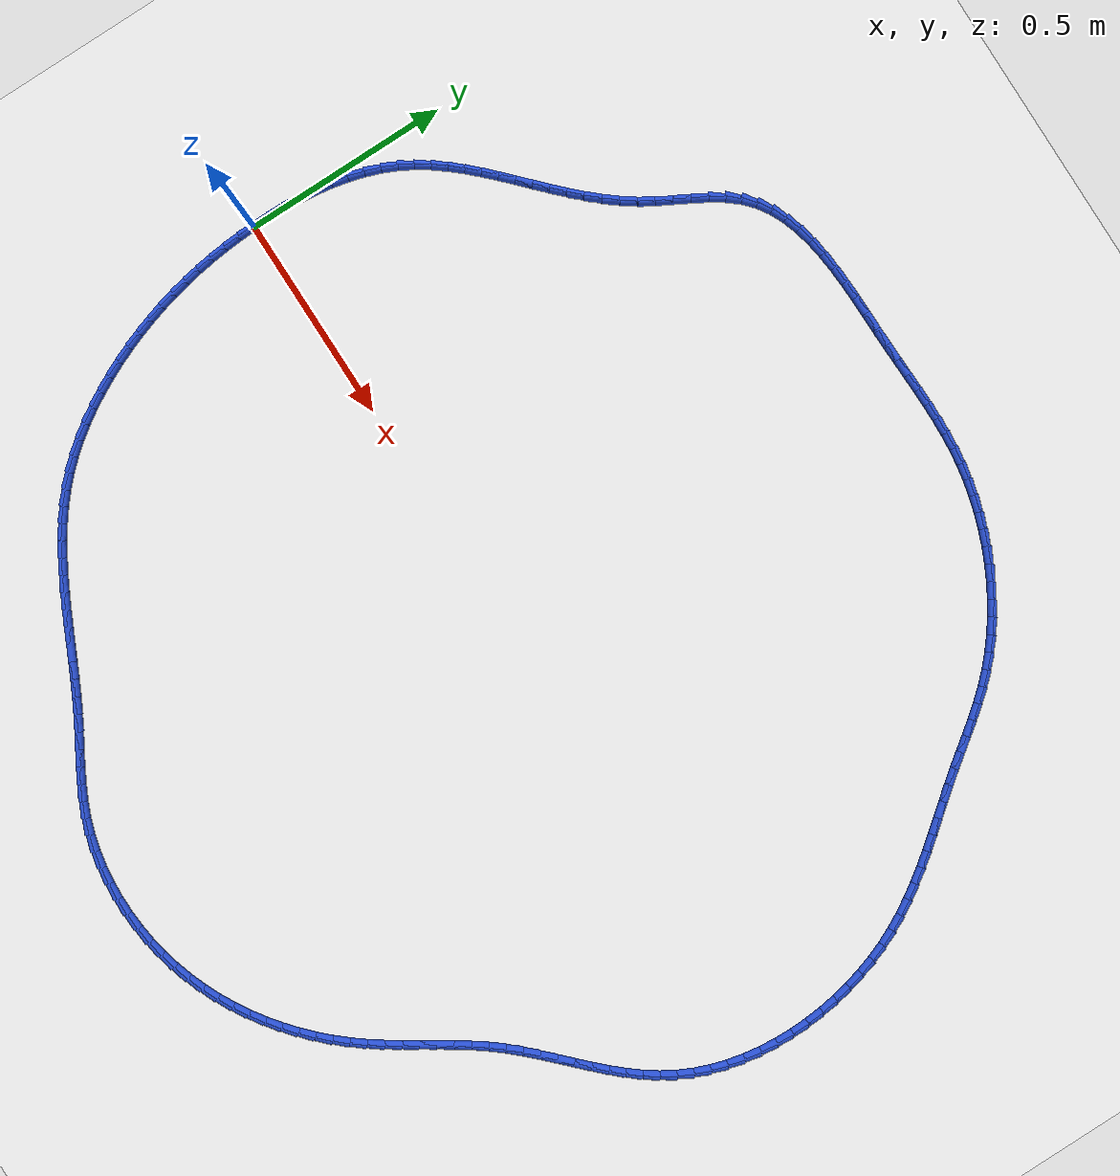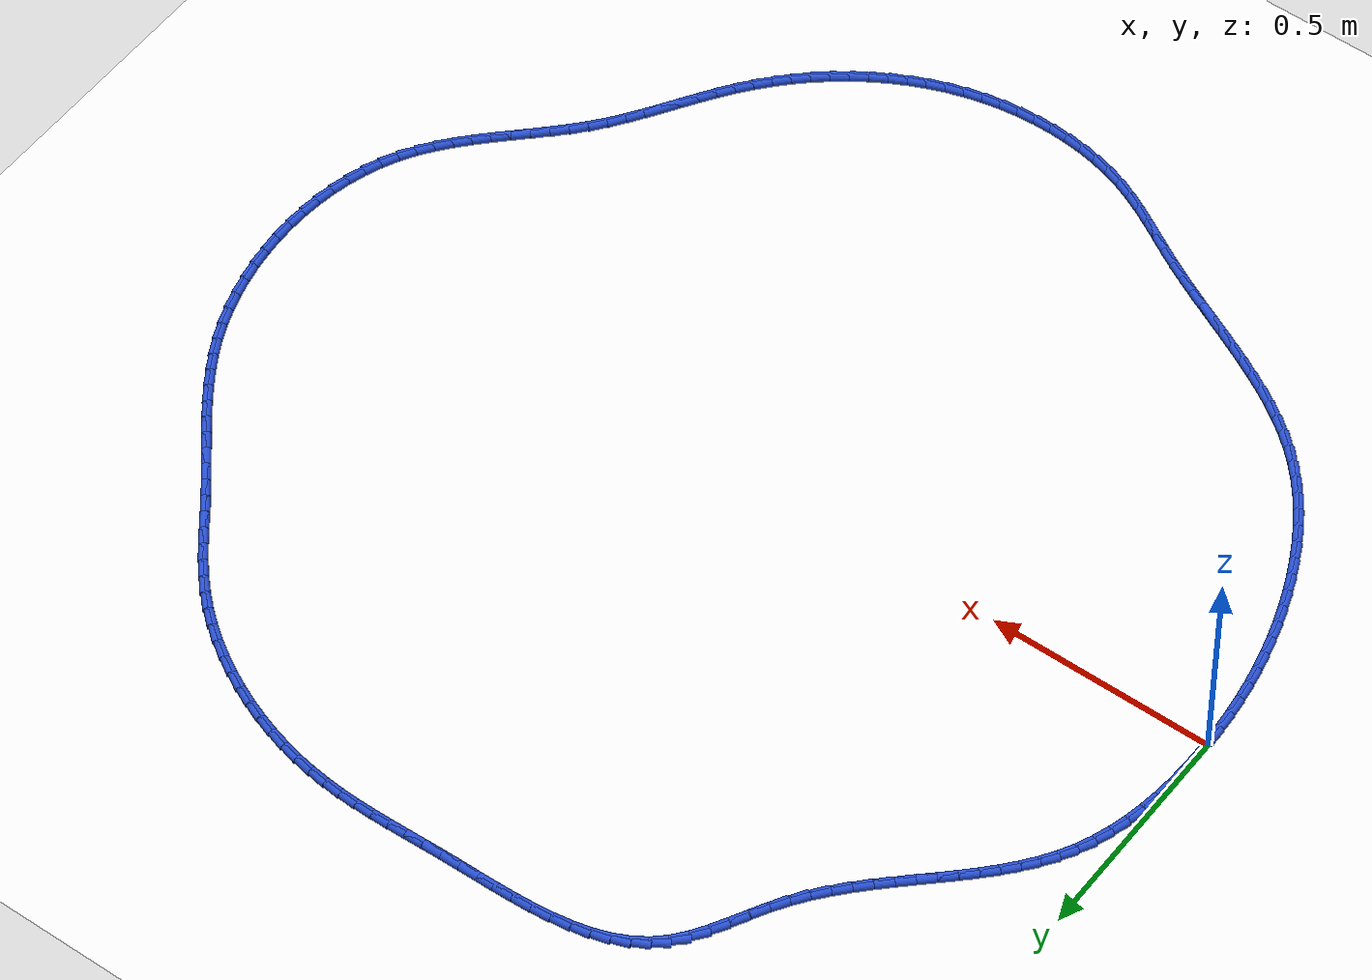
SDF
<sdf version="1.6">
 <world name="default">
  <light name="sun" type="directional">
   <pose>0 0 10 0 -0 0</pose>
   <diffuse>0.8 0.8 0.8 1</diffuse>
   <specular>0.2 0.2 0.2 1</specular>
   <attenuation>
    <range>1000</range>
    <constant>0.9</constant>
    <linear>0.01</linear>
    <quadratic>0.001</quadratic>
   </attenuation>
   <direction>-0.5 0.1 -0.9</direction>
  </light>
  <model name="ground_plane">
   <static>1</static>
   <link name="link">
    <collision name="collision">
     <geometry><plane><normal>0 0 1</normal><size>100 100</size></plane></geometry>
     <surface><friction><ode><mu>100</mu><mu2>50</mu2></ode></friction></surface>
    </collision>
    <visual name="visual">
     <cast_shadows>0</cast_shadows>
     <geometry><plane><normal>0 0 1</normal><size>100 100</size></plane></geometry>
     <material>
      <script><uri>file://media/materials/scripts/gazebo.material</uri><name>Gazebo/WhiteGlow</name></script>
     </material>
    </visual>
   </link>
  </model>
  <gravity>0 0 -9.8</gravity>
  <magnetic_field>6e-06 2.3e-05 -4.2e-05</magnetic_field>
  <atmosphere type="adiabatic"/>
  <physics name="default_physics" default="0" type="ode">
   <max_step_size>0.001</max_step_size>
   <real_time_factor>1</real_time_factor>
   <real_time_update_rate>1000</real_time_update_rate>
  </physics>
  <scene><ambient>0.4 0.4 0.4 1</ambient><background>0.7 0.7 0.7 1</background><shadows>1</shadows></scene>
  <spherical_coordinates>
   <surface_model>EARTH_WGS84</surface_model>
   <latitude_deg>0</latitude_deg>
   <longitude_deg>0</longitude_deg>
   <elevation>0</elevation>
   <heading_deg>0</heading_deg>
  </spherical_coordinates>
  <model name="line">
   <link name="link_0">
    <pose>5.204170427930421e-18 2.7755575615628914e-17 0.01 0 1.57 -1.560474673501116</pose>
    <collision name="collision">
     <geometry><cylinder><radius>0.01</radius><length>0.08</length></cylinder></geometry>
    </collision>
    <visual name="visual">
     <material>
      <script><name>Gazebo/Blue</name><uri>file://media/materials/scripts/gazebo.material</uri></script>
     </material>
     <geometry><cylinder><radius>0.01</radius><length>0.08</length></cylinder></geometry>
    </visual>
   </link>
   <link name="link_1">
    <pose>-0.00041939425661725123 0.040631025957992235 0.01 0 1.57 1.5458353956558755</pose>
    <collision name="collision">
     <geometry><cylinder><radius>0.01</radius><length>0.08</length></cylinder></geometry>
    </collision>
    <visual name="visual">
     <material>
      <script><name>Gazebo/Blue</name><uri>file://media/materials/scripts/gazebo.material</uri></script>
     </material>
     <geometry><cylinder><radius>0.01</radius><length>0.08</length></cylinder></geometry>
    </visual>
   </link>
   <link name="link_2">
    <pose>0.0005989403063009725 0.08141969117231324 0.01 0 1.57 1.5063570734725502</pose>
    <collision name="collision">
     <geometry><cylinder><radius>0.01</radius><length>0.08</length></cylinder></geometry>
    </collision>
    <visual name="visual">
     <material>
      <script><name>Gazebo/Blue</name><uri>file://media/materials/scripts/gazebo.material</uri></script>
     </material>
     <geometry><cylinder><radius>0.01</radius><length>0.08</length></cylinder></geometry>
    </visual>
   </link>
   <link name="link_3">
    <pose>0.0032256557730024477 0.12212591579390611 0.01 0 1.57 1.4621289086431264</pose>
    <collision name="collision">
     <geometry><cylinder><radius>0.01</radius><length>0.08</length></cylinder></geometry>
    </collision>
    <visual name="visual">
     <material>
      <script><name>Gazebo/Blue</name><uri>file://media/materials/scripts/gazebo.material</uri></script>
     </material>
     <geometry><cylinder><radius>0.01</radius><length>0.08</length></cylinder></geometry>
    </visual>
   </link>
   <link name="link_4">
    <pose>0.007631404227734949 0.16250961997371421 0.01 0 1.57 1.412531463375703</pose>
    <collision name="collision">
     <geometry><cylinder><radius>0.01</radius><length>0.08</length></cylinder></geometry>
    </collision>
    <visual name="visual">
     <material>
      <script><name>Gazebo/Blue</name><uri>file://media/materials/scripts/gazebo.material</uri></script>
     </material>
     <geometry><cylinder><radius>0.01</radius><length>0.08</length></cylinder></geometry>
    </visual>
   </link>
   <link name="link_5">
    <pose>0.013986837754746233 0.20233072386268047 0.01 0 1.57 1.3568946053607458</pose>
    <collision name="collision">
     <geometry><cylinder><radius>0.01</radius><length>0.08</length></cylinder></geometry>
    </collision>
    <visual name="visual">
     <material>
      <script><name>Gazebo/Blue</name><uri>file://media/materials/scripts/gazebo.material</uri></script>
     </material>
     <geometry><cylinder><radius>0.01</radius><length>0.08</length></cylinder></geometry>
    </visual>
   </link>
   <link name="link_6">
    <pose>0.022462608438284078 0.2413491476117482 0.01 0 1.57 1.2945289646001075</pose>
    <collision name="collision">
     <geometry><cylinder><radius>0.01</radius><length>0.08</length></cylinder></geometry>
    </collision>
    <visual name="visual">
     <material>
      <script><name>Gazebo/Blue</name><uri>file://media/materials/scripts/gazebo.material</uri></script>
     </material>
     <geometry><cylinder><radius>0.01</radius><length>0.08</length></cylinder></geometry>
    </visual>
   </link>
   <link name="link_7">
    <pose>0.03322936836259625 0.2793248113718606 0.01 0 1.57 1.2247827890572607</pose>
    <collision name="collision">
     <geometry><cylinder><radius>0.01</radius><length>0.08</length></cylinder></geometry>
    </collision>
    <visual name="visual">
     <material>
      <script><name>Gazebo/Blue</name><uri>file://media/materials/scripts/gazebo.material</uri></script>
     </material>
     <geometry><cylinder><radius>0.01</radius><length>0.08</length></cylinder></geometry>
    </visual>
   </link>
   <link name="link_8">
    <pose>0.04645776961193051 0.31601763529396065 0.01 0 1.57 1.1471331357674486</pose>
    <collision name="collision">
     <geometry><cylinder><radius>0.01</radius><length>0.08</length></cylinder></geometry>
    </collision>
    <visual name="visual">
     <material>
      <script><name>Gazebo/Blue</name><uri>file://media/materials/scripts/gazebo.material</uri></script>
     </material>
     <geometry><cylinder><radius>0.01</radius><length>0.08</length></cylinder></geometry>
    </visual>
   </link>
   <link name="link_9">
    <pose>0.062318464270534626 0.3511875395289916 0.01 0 1.57 1.0624089288465834</pose>
    <collision name="collision">
     <geometry><cylinder><radius>0.01</radius><length>0.08</length></cylinder></geometry>
    </collision>
    <visual name="visual">
     <material>
      <script><name>Gazebo/Blue</name><uri>file://media/materials/scripts/gazebo.material</uri></script>
     </material>
     <geometry><cylinder><radius>0.01</radius><length>0.08</length></cylinder></geometry>
    </visual>
   </link>
   <link name="link_10">
    <pose>0.08095076888299968 0.3846240996175285 0.01 0 1.57 0.9821560411608776</pose>
    <collision name="collision">
     <geometry><cylinder><radius>0.01</radius><length>0.08</length></cylinder></geometry>
    </collision>
    <visual name="visual">
     <material>
      <script><name>Gazebo/Blue</name><uri>file://media/materials/scripts/gazebo.material</uri></script>
     </material>
     <geometry><cylinder><radius>0.01</radius><length>0.08</length></cylinder></geometry>
    </visual>
   </link>
   <link name="link_11">
    <pose>0.10217593487862389 0.4164179021893304 0.01 0 1.57 0.9139354953950708</pose>
    <collision name="collision">
     <geometry><cylinder><radius>0.01</radius><length>0.08</length></cylinder></geometry>
    </collision>
    <visual name="visual">
     <material>
      <script><name>Gazebo/Blue</name><uri>file://media/materials/scripts/gazebo.material</uri></script>
     </material>
     <geometry><cylinder><radius>0.01</radius><length>0.08</length></cylinder></geometry>
    </visual>
   </link>
   <link name="link_12">
    <pose>0.12563001481334368 0.446834802748064 0.01 0 1.57 0.8583358593702851</pose>
    <collision name="collision">
     <geometry><cylinder><radius>0.01</radius><length>0.08</length></cylinder></geometry>
    </collision>
    <visual name="visual">
     <material>
      <script><name>Gazebo/Blue</name><uri>file://media/materials/scripts/gazebo.material</uri></script>
     </material>
     <geometry><cylinder><radius>0.01</radius><length>0.08</length></cylinder></geometry>
    </visual>
   </link>
   <link name="link_13">
    <pose>0.1509467605462268 0.4761428341354215 0.01 0 1.57 0.8153100233511009</pose>
    <collision name="collision">
     <geometry><cylinder><radius>0.01</radius><length>0.08</length></cylinder></geometry>
    </collision>
    <visual name="visual">
     <material>
      <script><name>Gazebo/Blue</name><uri>file://media/materials/scripts/gazebo.material</uri></script>
     </material>
     <geometry><cylinder><radius>0.01</radius><length>0.08</length></cylinder></geometry>
    </visual>
   </link>
   <link name="link_14">
    <pose>0.17775992393634085 0.5046100291930952 0.01 0 1.57 0.7845216713008123</pose>
    <collision name="collision">
     <geometry><cylinder><radius>0.01</radius><length>0.08</length></cylinder></geometry>
    </collision>
    <visual name="visual">
     <material>
      <script><name>Gazebo/Blue</name><uri>file://media/materials/scripts/gazebo.material</uri></script>
     </material>
     <geometry><cylinder><radius>0.01</radius><length>0.08</length></cylinder></geometry>
    </visual>
   </link>
   <link name="link_15">
    <pose>0.2057032568427537 0.5325044207627777 0.01 0 1.57 0.7655482772136365</pose>
    <collision name="collision">
     <geometry><cylinder><radius>0.01</radius><length>0.08</length></cylinder></geometry>
    </collision>
    <visual name="visual">
     <material>
      <script><name>Gazebo/Blue</name><uri>file://media/materials/scripts/gazebo.material</uri></script>
     </material>
     <geometry><cylinder><radius>0.01</radius><length>0.08</length></cylinder></geometry>
    </visual>
   </link>
   <link name="link_16">
    <pose>0.2344105111245332 0.5600940416861612 0.01 0 1.57 0.7580117123435444</pose>
    <collision name="collision">
     <geometry><cylinder><radius>0.01</radius><length>0.08</length></cylinder></geometry>
    </collision>
    <visual name="visual">
     <material>
      <script><name>Gazebo/Blue</name><uri>file://media/materials/scripts/gazebo.material</uri></script>
     </material>
     <geometry><cylinder><radius>0.01</radius><length>0.08</length></cylinder></geometry>
    </visual>
   </link>
   <link name="link_17">
    <pose>0.26351543864074695 0.5876469248049384 0.01 0 1.57 0.7616471518119733</pose>
    <collision name="collision">
     <geometry><cylinder><radius>0.01</radius><length>0.08</length></cylinder></geometry>
    </collision>
    <visual name="visual">
     <material>
      <script><name>Gazebo/Blue</name><uri>file://media/materials/scripts/gazebo.material</uri></script>
     </material>
     <geometry><cylinder><radius>0.01</radius><length>0.08</length></cylinder></geometry>
    </visual>
   </link>
   <link name="link_18">
    <pose>0.29265179125046276 0.6154311029608015 0.01 0 1.57 0.7763238183701574</pose>
    <collision name="collision">
     <geometry><cylinder><radius>0.01</radius><length>0.08</length></cylinder></geometry>
    </collision>
    <visual name="visual">
     <material>
      <script><name>Gazebo/Blue</name><uri>file://media/materials/scripts/gazebo.material</uri></script>
     </material>
     <geometry><cylinder><radius>0.01</radius><length>0.08</length></cylinder></geometry>
    </visual>
   </link>
   <link name="link_19">
    <pose>0.32145332081274836 0.6437146089954429 0.01 0 1.57 0.802026313014735</pose>
    <collision name="collision">
     <geometry><cylinder><radius>0.01</radius><length>0.08</length></cylinder></geometry>
    </collision>
    <visual name="visual">
     <material>
      <script><name>Gazebo/Blue</name><uri>file://media/materials/scripts/gazebo.material</uri></script>
     </material>
     <geometry><cylinder><radius>0.01</radius><length>0.08</length></cylinder></geometry>
    </visual>
   </link>
   <link name="link_20">
    <pose>0.3495537791866714 0.6727654757505548 0.01 0 1.57 0.8387989102687063</pose>
    <collision name="collision">
     <geometry><cylinder><radius>0.01</radius><length>0.08</length></cylinder></geometry>
    </collision>
    <visual name="visual">
     <material>
      <script><name>Gazebo/Blue</name><uri>file://media/materials/scripts/gazebo.material</uri></script>
     </material>
     <geometry><cylinder><radius>0.01</radius><length>0.08</length></cylinder></geometry>
    </visual>
   </link>
   <link name="link_21">
    <pose>0.3765869182312999 0.7028517360678301 0.01 0 1.57 0.8866508350229066</pose>
    <collision name="collision">
     <geometry><cylinder><radius>0.01</radius><length>0.08</length></cylinder></geometry>
    </collision>
    <visual name="visual">
     <material>
      <script><name>Gazebo/Blue</name><uri>file://media/materials/scripts/gazebo.material</uri></script>
     </material>
     <geometry><cylinder><radius>0.01</radius><length>0.08</length></cylinder></geometry>
    </visual>
   </link>
   <link name="link_22">
    <pose>0.4021864898057013 0.7342414227889607 0.01 0 1.57 0.945421279363909</pose>
    <collision name="collision">
     <geometry><cylinder><radius>0.01</radius><length>0.08</length></cylinder></geometry>
    </collision>
    <visual name="visual">
     <material>
      <script><name>Gazebo/Blue</name><uri>file://media/materials/scripts/gazebo.material</uri></script>
     </material>
     <geometry><cylinder><radius>0.01</radius><length>0.08</length></cylinder></geometry>
    </visual>
   </link>
   <link name="link_23">
    <pose>0.4259862457689436 0.7672025687556392 0.01 0 1.57 1.0120313819367213</pose>
    <collision name="collision">
     <geometry><cylinder><radius>0.01</radius><length>0.08</length></cylinder></geometry>
    </collision>
    <visual name="visual">
     <material>
      <script><name>Gazebo/Blue</name><uri>file://media/materials/scripts/gazebo.material</uri></script>
     </material>
     <geometry><cylinder><radius>0.01</radius><length>0.08</length></cylinder></geometry>
    </visual>
   </link>
   <link name="link_24">
    <pose>0.44769590768977613 0.8019252303119604 0.01 0 1.57 1.0593090772187204</pose>
    <collision name="collision">
     <geometry><cylinder><radius>0.01</radius><length>0.08</length></cylinder></geometry>
    </collision>
    <visual name="visual">
     <material>
      <script><name>Gazebo/Blue</name><uri>file://media/materials/scripts/gazebo.material</uri></script>
     </material>
     <geometry><cylinder><radius>0.01</radius><length>0.08</length></cylinder></geometry>
    </visual>
   </link>
   <link name="link_25">
    <pose>0.4678223544851671 0.8377812490384116 0.01 0 1.57 1.07231941583553</pose>
    <collision name="collision">
     <geometry><cylinder><radius>0.01</radius><length>0.08</length></cylinder></geometry>
    </collision>
    <visual name="visual">
     <material>
      <script><name>Gazebo/Blue</name><uri>file://media/materials/scripts/gazebo.material</uri></script>
     </material>
     <geometry><cylinder><radius>0.01</radius><length>0.08</length></cylinder></geometry>
    </visual>
   </link>
   <link name="link_26">
    <pose>0.4873486699594717 0.8736536823748919 0.01 0 1.57 1.0505722540732303</pose>
    <collision name="collision">
     <geometry><cylinder><radius>0.01</radius><length>0.08</length></cylinder></geometry>
    </collision>
    <visual name="visual">
     <material>
      <script><name>Gazebo/Blue</name><uri>file://media/materials/scripts/gazebo.material</uri></script>
     </material>
     <geometry><cylinder><radius>0.01</radius><length>0.08</length></cylinder></geometry>
    </visual>
   </link>
   <link name="link_27">
    <pose>0.5072643263870428 0.9084190305358298 0.01 0 1.57 0.9912541114067657</pose>
    <collision name="collision">
     <geometry><cylinder><radius>0.01</radius><length>0.08</length></cylinder></geometry>
    </collision>
    <visual name="visual">
     <material>
      <script><name>Gazebo/Blue</name><uri>file://media/materials/scripts/gazebo.material</uri></script>
     </material>
     <geometry><cylinder><radius>0.01</radius><length>0.08</length></cylinder></geometry>
    </visual>
   </link>
   <link name="link_28">
    <pose>0.5285587960422333 0.940953793735653 0.01 0 1.57 0.889441335161986</pose>
    <collision name="collision">
     <geometry><cylinder><radius>0.01</radius><length>0.08</length></cylinder></geometry>
    </collision>
    <visual name="visual">
     <material>
      <script><name>Gazebo/Blue</name><uri>file://media/materials/scripts/gazebo.material</uri></script>
     </material>
     <geometry><cylinder><radius>0.01</radius><length>0.08</length></cylinder></geometry>
    </visual>
   </link>
   <link name="link_29">
    <pose>0.5522215511993964 0.9701344721887895 0.01 0 1.57 0.7428690734591776</pose>
    <collision name="collision">
     <geometry><cylinder><radius>0.01</radius><length>0.08</length></cylinder></geometry>
    </collision>
    <visual name="visual">
     <material>
      <script><name>Gazebo/Blue</name><uri>file://media/materials/scripts/gazebo.material</uri></script>
     </material>
     <geometry><cylinder><radius>0.01</radius><length>0.08</length></cylinder></geometry>
    </visual>
   </link>
   <link name="link_30">
    <pose>0.5791879028655661 0.9948994117107092 0.01 0 1.57 0.5851730743979048</pose>
    <collision name="collision">
     <geometry><cylinder><radius>0.01</radius><length>0.08</length></cylinder></geometry>
    </collision>
    <visual name="visual">
     <material>
      <script><name>Gazebo/Blue</name><uri>file://media/materials/scripts/gazebo.material</uri></script>
     </material>
     <geometry><cylinder><radius>0.01</radius><length>0.08</length></cylinder></geometry>
    </visual>
   </link>
   <link name="link_31">
    <pose>0.6096235933495142 1.0150657122717237 0.01 0 1.57 0.44652051022033024</pose>
    <collision name="collision">
     <geometry><cylinder><radius>0.01</radius><length>0.08</length></cylinder></geometry>
    </collision>
    <visual name="visual">
     <material>
      <script><name>Gazebo/Blue</name><uri>file://media/materials/scripts/gazebo.material</uri></script>
     </material>
     <geometry><cylinder><radius>0.01</radius><length>0.08</length></cylinder></geometry>
    </visual>
   </link>
   <link name="link_32">
    <pose>0.6431221680921743 1.0311038532949905 0.01 0 1.57 0.3304124110964919</pose>
    <collision name="collision">
     <geometry><cylinder><radius>0.01</radius><length>0.08</length></cylinder></geometry>
    </collision>
    <visual name="visual">
     <material>
      <script><name>Gazebo/Blue</name><uri>file://media/materials/scripts/gazebo.material</uri></script>
     </material>
     <geometry><cylinder><radius>0.01</radius><length>0.08</length></cylinder></geometry>
    </visual>
   </link>
   <link name="link_33">
    <pose>0.6792635755675412 1.0434998402914855 0.01 0 1.57 0.2363441870183302</pose>
    <collision name="collision">
     <geometry><cylinder><radius>0.01</radius><length>0.08</length></cylinder></geometry>
    </collision>
    <visual name="visual">
     <material>
      <script><name>Gazebo/Blue</name><uri>file://media/materials/scripts/gazebo.material</uri></script>
     </material>
     <geometry><cylinder><radius>0.01</radius><length>0.08</length></cylinder></geometry>
    </visual>
   </link>
   <link name="link_34">
    <pose>0.7176277642496095 1.0527396787721834 0.01 0 1.57 0.16212432237030058</pose>
    <collision name="collision">
     <geometry><cylinder><radius>0.01</radius><length>0.08</length></cylinder></geometry>
    </collision>
    <visual name="visual">
     <material>
      <script><name>Gazebo/Blue</name><uri>file://media/materials/scripts/gazebo.material</uri></script>
     </material>
     <geometry><cylinder><radius>0.01</radius><length>0.08</length></cylinder></geometry>
    </visual>
   </link>
   <link name="link_35">
    <pose>0.7577946826123735 1.0593093742480604 0.01 0 1.57 0.10516058293300554</pose>
    <collision name="collision">
     <geometry><cylinder><radius>0.01</radius><length>0.08</length></cylinder></geometry>
    </collision>
    <visual name="visual">
     <material>
      <script><name>Gazebo/Blue</name><uri>file://media/materials/scripts/gazebo.material</uri></script>
     </material>
     <geometry><cylinder><radius>0.01</radius><length>0.08</length></cylinder></geometry>
    </visual>
   </link>
   <link name="link_36">
    <pose>0.7993442791298286 1.0636949322300915 0.01 0 1.57 0.0631313665549837</pose>
    <collision name="collision">
     <geometry><cylinder><radius>0.01</radius><length>0.08</length></cylinder></geometry>
    </collision>
    <visual name="visual">
     <material>
      <script><name>Gazebo/Blue</name><uri>file://media/materials/scripts/gazebo.material</uri></script>
     </material>
     <geometry><cylinder><radius>0.01</radius><length>0.08</length></cylinder></geometry>
    </visual>
   </link>
   <link name="link_37">
    <pose>0.8418565022759693 1.0663823582292529 0.01 0 1.57 0.03425222261847</pose>
    <collision name="collision">
     <geometry><cylinder><radius>0.01</radius><length>0.08</length></cylinder></geometry>
    </collision>
    <visual name="visual">
     <material>
      <script><name>Gazebo/Blue</name><uri>file://media/materials/scripts/gazebo.material</uri></script>
     </material>
     <geometry><cylinder><radius>0.01</radius><length>0.08</length></cylinder></geometry>
    </visual>
   </link>
   <link name="link_38">
    <pose>0.8849113005247897 1.0678576577565195 0.01 0 1.57 0.017349464130928447</pose>
    <collision name="collision">
     <geometry><cylinder><radius>0.01</radius><length>0.08</length></cylinder></geometry>
    </collision>
    <visual name="visual">
     <material>
      <script><name>Gazebo/Blue</name><uri>file://media/materials/scripts/gazebo.material</uri></script>
     </material>
     <geometry><cylinder><radius>0.01</radius><length>0.08</length></cylinder></geometry>
    </visual>
   </link>
   <link name="link_39">
    <pose>0.9280886223502853 1.0686068363228671 0.01 0 1.57 0.011871307122232182</pose>
    <collision name="collision">
     <geometry><cylinder><radius>0.01</radius><length>0.08</length></cylinder></geometry>
    </collision>
    <visual name="visual">
     <material>
      <script><name>Gazebo/Blue</name><uri>file://media/materials/scripts/gazebo.material</uri></script>
     </material>
     <geometry><cylinder><radius>0.01</radius><length>0.08</length></cylinder></geometry>
    </visual>
   </link>
   <link name="link_40">
    <pose>0.9709684162264505 1.0691158994392713 0.01 0 1.57 0.01777152209160328</pose>
    <collision name="collision">
     <geometry><cylinder><radius>0.01</radius><length>0.08</length></cylinder></geometry>
    </collision>
    <visual name="visual">
     <material>
      <script><name>Gazebo/Blue</name><uri>file://media/materials/scripts/gazebo.material</uri></script>
     </material>
     <geometry><cylinder><radius>0.01</radius><length>0.08</length></cylinder></geometry>
    </visual>
   </link>
   <link name="link_41">
    <pose>1.0131344743179589 1.0698653333709778 0.01 0 1.57 0.028245616850283622</pose>
    <collision name="collision">
     <geometry><cylinder><radius>0.01</radius><length>0.08</length></cylinder></geometry>
    </collision>
    <visual name="visual">
     <material>
      <script><name>Gazebo/Blue</name><uri>file://media/materials/scripts/gazebo.material</uri></script>
     </material>
     <geometry><cylinder><radius>0.01</radius><length>0.08</length></cylinder></geometry>
    </visual>
   </link>
   <link name="link_42">
    <pose>1.0543829213023512 1.071030731140544 0.01 0 1.57 0.032102971587393156</pose>
    <collision name="collision">
     <geometry><cylinder><radius>0.01</radius><length>0.08</length></cylinder></geometry>
    </collision>
    <visual name="visual">
     <material>
      <script><name>Gazebo/Blue</name><uri>file://media/materials/scripts/gazebo.material</uri></script>
     </material>
     <geometry><cylinder><radius>0.01</radius><length>0.08</length></cylinder></geometry>
    </visual>
   </link>
   <link name="link_43">
    <pose>1.0948288908993886 1.072329613193624 0.01 0 1.57 0.027946312179015293</pose>
    <collision name="collision">
     <geometry><cylinder><radius>0.01</radius><length>0.08</length></cylinder></geometry>
    </collision>
    <visual name="visual">
     <material>
      <script><name>Gazebo/Blue</name><uri>file://media/materials/scripts/gazebo.material</uri></script>
     </material>
     <geometry><cylinder><radius>0.01</radius><length>0.08</length></cylinder></geometry>
    </visual>
   </link>
   <link name="link_44">
    <pose>1.1346138103363617 1.0734417445108073 0.01 0 1.57 0.015410495042441434</pose>
    <collision name="collision">
     <geometry><cylinder><radius>0.01</radius><length>0.08</length></cylinder></geometry>
    </collision>
    <visual name="visual">
     <material>
      <script><name>Gazebo/Blue</name><uri>file://media/materials/scripts/gazebo.material</uri></script>
     </material>
     <geometry><cylinder><radius>0.01</radius><length>0.08</length></cylinder></geometry>
    </visual>
   </link>
   <link name="link_45">
    <pose>1.173879106840559 1.0740468900726836 0.01 0 1.57 -0.0057107059708064066</pose>
    <collision name="collision">
     <geometry><cylinder><radius>0.01</radius><length>0.08</length></cylinder></geometry>
    </collision>
    <visual name="visual">
     <material>
      <script><name>Gazebo/Blue</name><uri>file://media/materials/scripts/gazebo.material</uri></script>
     </material>
     <geometry><cylinder><radius>0.01</radius><length>0.08</length></cylinder></geometry>
    </visual>
   </link>
   <link name="link_46">
    <pose>1.21276620763927 1.0738248148598422 0.01 0 1.57 -0.035419055421516854</pose>
    <collision name="collision">
     <geometry><cylinder><radius>0.01</radius><length>0.08</length></cylinder></geometry>
    </collision>
    <visual name="visual">
     <material>
      <script><name>Gazebo/Blue</name><uri>file://media/materials/scripts/gazebo.material</uri></script>
     </material>
     <geometry><cylinder><radius>0.01</radius><length>0.08</length></cylinder></geometry>
    </visual>
   </link>
   <link name="link_47">
    <pose>1.2514165399597839 1.0724552838528723 0.01 0 1.57 -0.07345655687997786</pose>
    <collision name="collision">
     <geometry><cylinder><radius>0.01</radius><length>0.08</length></cylinder></geometry>
    </collision>
    <visual name="visual">
     <material>
      <script><name>Gazebo/Blue</name><uri>file://media/materials/scripts/gazebo.material</uri></script>
     </material>
     <geometry><cylinder><radius>0.01</radius><length>0.08</length></cylinder></geometry>
    </visual>
   </link>
   <link name="link_48">
    <pose>1.2899715310293896 1.0696180620323636 0.01 0 1.57 -0.1192505983145177</pose>
    <collision name="collision">
     <geometry><cylinder><radius>0.01</radius><length>0.08</length></cylinder></geometry>
    </collision>
    <visual name="visual">
     <material>
      <script><name>Gazebo/Blue</name><uri>file://media/materials/scripts/gazebo.material</uri></script>
     </material>
     <geometry><cylinder><radius>0.01</radius><length>0.08</length></cylinder></geometry>
    </visual>
   </link>
   <link name="link_49">
    <pose>1.3285726071095398 1.064992915519093 0.01 0 1.57 -0.17047003964254903</pose>
    <collision name="collision">
     <geometry><cylinder><radius>0.01</radius><length>0.08</length></cylinder></geometry>
    </collision>
    <visual name="visual">
     <material>
      <script><name>Gazebo/Blue</name><uri>file://media/materials/scripts/gazebo.material</uri></script>
     </material>
     <geometry><cylinder><radius>0.01</radius><length>0.08</length></cylinder></geometry>
    </visual>
   </link>
   <link name="link_50">
    <pose>1.3673054528960336 1.0583254143526675 0.01 0 1.57 -0.22140598250828952</pose>
    <collision name="collision">
     <geometry><cylinder><radius>0.01</radius><length>0.08</length></cylinder></geometry>
    </collision>
    <visual name="visual">
     <material>
      <script><name>Gazebo/Blue</name><uri>file://media/materials/scripts/gazebo.material</uri></script>
     </material>
     <geometry><cylinder><radius>0.01</radius><length>0.08</length></cylinder></geometry>
    </visual>
   </link>
   <link name="link_51">
    <pose>1.406049852251417 1.049604198202317 0.01 0 1.57 -0.27121711104897983</pose>
    <collision name="collision">
     <geometry><cylinder><radius>0.01</radius><length>0.08</length></cylinder></geometry>
    </collision>
    <visual name="visual">
     <material>
      <script><name>Gazebo/Blue</name><uri>file://media/materials/scripts/gazebo.material</uri></script>
     </material>
     <geometry><cylinder><radius>0.01</radius><length>0.08</length></cylinder></geometry>
    </visual>
   </link>
   <link name="link_52">
    <pose>1.4446380582624538 1.0388740176712756 0.01 0 1.57 -0.3203301551867465</pose>
    <collision name="collision">
     <geometry><cylinder><radius>0.01</radius><length>0.08</length></cylinder></geometry>
    </collision>
    <visual name="visual">
     <material>
      <script><name>Gazebo/Blue</name><uri>file://media/materials/scripts/gazebo.material</uri></script>
     </material>
     <geometry><cylinder><radius>0.01</radius><length>0.08</length></cylinder></geometry>
    </visual>
   </link>
   <link name="link_53">
    <pose>1.4829023240159038 1.0261796233627778 0.01 0 1.57 -0.36915438253753846</pose>
    <collision name="collision">
     <geometry><cylinder><radius>0.01</radius><length>0.08</length></cylinder></geometry>
    </collision>
    <visual name="visual">
     <material>
      <script><name>Gazebo/Blue</name><uri>file://media/materials/scripts/gazebo.material</uri></script>
     </material>
     <geometry><cylinder><radius>0.01</radius><length>0.08</length></cylinder></geometry>
    </visual>
   </link>
   <link name="link_54">
    <pose>1.5206749025985302 1.0115657658800576 0.01 0 1.57 -0.41808570130019196</pose>
    <collision name="collision">
     <geometry><cylinder><radius>0.01</radius><length>0.08</length></cylinder></geometry>
    </collision>
    <visual name="visual">
     <material>
      <script><name>Gazebo/Blue</name><uri>file://media/materials/scripts/gazebo.material</uri></script>
     </material>
     <geometry><cylinder><radius>0.01</radius><length>0.08</length></cylinder></geometry>
    </visual>
   </link>
   <link name="link_55">
    <pose>1.5577880470970946 0.995077195826349 0.01 0 1.57 -0.4675104874489359</pose>
    <collision name="collision">
     <geometry><cylinder><radius>0.01</radius><length>0.08</length></cylinder></geometry>
    </collision>
    <visual name="visual">
     <material>
      <script><name>Gazebo/Blue</name><uri>file://media/materials/scripts/gazebo.material</uri></script>
     </material>
     <geometry><cylinder><radius>0.01</radius><length>0.08</length></cylinder></geometry>
    </visual>
   </link>
   <link name="link_56">
    <pose>1.5940740105983588 0.9767586638048867 0.01 0 1.57 -0.5178087026499977</pose>
    <collision name="collision">
     <geometry><cylinder><radius>0.01</radius><length>0.08</length></cylinder></geometry>
    </collision>
    <visual name="visual">
     <material>
      <script><name>Gazebo/Blue</name><uri>file://media/materials/scripts/gazebo.material</uri></script>
     </material>
     <geometry><cylinder><radius>0.01</radius><length>0.08</length></cylinder></geometry>
    </visual>
   </link>
   <link name="link_57">
    <pose>1.6293650461890847 0.9566549204189045 0.01 0 1.57 -0.5693558706678074</pose>
    <collision name="collision">
     <geometry><cylinder><radius>0.01</radius><length>0.08</length></cylinder></geometry>
    </collision>
    <visual name="visual">
     <material>
      <script><name>Gazebo/Blue</name><uri>file://media/materials/scripts/gazebo.material</uri></script>
     </material>
     <geometry><cylinder><radius>0.01</radius><length>0.08</length></cylinder></geometry>
    </visual>
   </link>
   <link name="link_58">
    <pose>1.6634934069560345 0.9348107162716368 0.01 0 1.57 -0.622523420351744</pose>
    <collision name="collision">
     <geometry><cylinder><radius>0.01</radius><length>0.08</length></cylinder></geometry>
    </collision>
    <visual name="visual">
     <material>
      <script><name>Gazebo/Blue</name><uri>file://media/materials/scripts/gazebo.material</uri></script>
     </material>
     <geometry><cylinder><radius>0.01</radius><length>0.08</length></cylinder></geometry>
    </visual>
   </link>
   <link name="link_59">
    <pose>1.6962913459859688 0.9112708019663178 0.01 0 1.57 -0.6776767998014511</pose>
    <collision name="collision">
     <geometry><cylinder><radius>0.01</radius><length>0.08</length></cylinder></geometry>
    </collision>
    <visual name="visual">
     <material>
      <script><name>Gazebo/Blue</name><uri>file://media/materials/scripts/gazebo.material</uri></script>
     </material>
     <geometry><cylinder><radius>0.01</radius><length>0.08</length></cylinder></geometry>
    </visual>
   </link>
   <link name="link_60">
    <pose>1.727591116365651 0.8860799281061817 0.01 0 1.57 -0.7351706431296637</pose>
    <collision name="collision">
     <geometry><cylinder><radius>0.01</radius><length>0.08</length></cylinder></geometry>
    </collision>
    <visual name="visual">
     <material>
      <script><name>Gazebo/Blue</name><uri>file://media/materials/scripts/gazebo.material</uri></script>
     </material>
     <geometry><cylinder><radius>0.01</radius><length>0.08</length></cylinder></geometry>
    </visual>
   </link>
   <link name="link_61">
    <pose>1.7572249711818426 0.8592828452944626 0.01 0 1.57 -0.7950179411912113</pose>
    <collision name="collision">
     <geometry><cylinder><radius>0.01</radius><length>0.08</length></cylinder></geometry>
    </collision>
    <visual name="visual">
     <material>
      <script><name>Gazebo/Blue</name><uri>file://media/materials/scripts/gazebo.material</uri></script>
     </material>
     <geometry><cylinder><radius>0.01</radius><length>0.08</length></cylinder></geometry>
    </visual>
   </link>
   <link name="link_62">
    <pose>1.785037131989895 0.8309303765635527 0.01 0 1.57 -0.8494318743351492</pose>
    <collision name="collision">
     <geometry><cylinder><radius>0.01</radius><length>0.08</length></cylinder></geometry>
    </collision>
    <visual name="visual">
     <material>
      <script><name>Gazebo/Blue</name><uri>file://media/materials/scripts/gazebo.material</uri></script>
     </material>
     <geometry><cylinder><radius>0.01</radius><length>0.08</length></cylinder></geometry>
    </visual>
   </link>
   <link name="link_63">
    <pose>1.8111650797487953 0.8012221356570319 0.01 0 1.57 -0.8898018991293719</pose>
    <collision name="collision">
     <geometry><cylinder><radius>0.01</radius><length>0.08</length></cylinder></geometry>
    </collision>
    <visual name="visual">
     <material>
      <script><name>Gazebo/Blue</name><uri>file://media/materials/scripts/gazebo.material</uri></script>
     </material>
     <geometry><cylinder><radius>0.01</radius><length>0.08</length></cylinder></geometry>
    </visual>
   </link>
   <link name="link_64">
    <pose>1.8360499085437387 0.7705117801868624 0.01 0 1.57 -0.9154983917307732</pose>
    <collision name="collision">
     <geometry><cylinder><radius>0.01</radius><length>0.08</length></cylinder></geometry>
    </collision>
    <visual name="visual">
     <material>
      <script><name>Gazebo/Blue</name><uri>file://media/materials/scripts/gazebo.material</uri></script>
     </material>
     <geometry><cylinder><radius>0.01</radius><length>0.08</length></cylinder></geometry>
    </visual>
   </link>
   <link name="link_65">
    <pose>1.860146752454534 0.7391600912221141 0.01 0 1.57 -0.9264902060715831</pose>
    <collision name="collision">
     <geometry><cylinder><radius>0.01</radius><length>0.08</length></cylinder></geometry>
    </collision>
    <visual name="visual">
     <material>
      <script><name>Gazebo/Blue</name><uri>file://media/materials/scripts/gazebo.material</uri></script>
     </material>
     <geometry><cylinder><radius>0.01</radius><length>0.08</length></cylinder></geometry>
    </visual>
   </link>
   <link name="link_66">
    <pose>1.8839107455609876 0.7075278498318556 0.01 0 1.57 -0.9228019884938927</pose>
    <collision name="collision">
     <geometry><cylinder><radius>0.01</radius><length>0.08</length></cylinder></geometry>
    </collision>
    <visual name="visual">
     <material>
      <script><name>Gazebo/Blue</name><uri>file://media/materials/scripts/gazebo.material</uri></script>
     </material>
     <geometry><cylinder><radius>0.01</radius><length>0.08</length></cylinder></geometry>
    </visual>
   </link>
   <link name="link_67">
    <pose>1.9077970219429063 0.6759758370851571 0.01 0 1.57 -0.9066860911887052</pose>
    <collision name="collision">
     <geometry><cylinder><radius>0.01</radius><length>0.08</length></cylinder></geometry>
    </collision>
    <visual name="visual">
     <material>
      <script><name>Gazebo/Blue</name><uri>file://media/materials/scripts/gazebo.material</uri></script>
     </material>
     <geometry><cylinder><radius>0.01</radius><length>0.08</length></cylinder></geometry>
    </visual>
   </link>
   <link name="link_68">
    <pose>1.9321906101087032 0.6448103667128161 0.01 0 1.57 -0.8928430830756112</pose>
    <collision name="collision">
     <geometry><cylinder><radius>0.01</radius><length>0.08</length></cylinder></geometry>
    </collision>
    <visual name="visual">
     <material>
      <script><name>Gazebo/Blue</name><uri>file://media/materials/scripts/gazebo.material</uri></script>
     </material>
     <geometry><cylinder><radius>0.01</radius><length>0.08</length></cylinder></geometry>
    </visual>
   </link>
   <link name="link_69">
    <pose>1.957017099077859 0.6139807987034206 0.01 0 1.57 -0.8871869909910638</pose>
    <collision name="collision">
     <geometry><cylinder><radius>0.01</radius><length>0.08</length></cylinder></geometry>
    </collision>
    <visual name="visual">
     <material>
      <script><name>Gazebo/Blue</name><uri>file://media/materials/scripts/gazebo.material</uri></script>
     </material>
     <geometry><cylinder><radius>0.01</radius><length>0.08</length></cylinder></geometry>
    </visual>
   </link>
   <link name="link_70">
    <pose>1.9820170685810303 0.5832927532069488 0.01 0 1.57 -0.8897308028658836</pose>
    <collision name="collision">
     <geometry><cylinder><radius>0.01</radius><length>0.08</length></cylinder></geometry>
    </collision>
    <visual name="visual">
     <material>
      <script><name>Gazebo/Blue</name><uri>file://media/materials/scripts/gazebo.material</uri></script>
     </material>
     <geometry><cylinder><radius>0.01</radius><length>0.08</length></cylinder></geometry>
    </visual>
   </link>
   <link name="link_71">
    <pose>2.006930590625704 0.5525514559064474 0.01 0 1.57 -0.9004846343471631</pose>
    <collision name="collision">
     <geometry><cylinder><radius>0.01</radius><length>0.08</length></cylinder></geometry>
    </collision>
    <visual name="visual">
     <material>
      <script><name>Gazebo/Blue</name><uri>file://media/materials/scripts/gazebo.material</uri></script>
     </material>
     <geometry><cylinder><radius>0.01</radius><length>0.08</length></cylinder></geometry>
    </visual>
   </link>
   <link name="link_72">
    <pose>2.0314977372193663 0.5215621324849643 0.01 0 1.57 -0.9194668621629304</pose>
    <collision name="collision">
     <geometry><cylinder><radius>0.01</radius><length>0.08</length></cylinder></geometry>
    </collision>
    <visual name="visual">
     <material>
      <script><name>Gazebo/Blue</name><uri>file://media/materials/scripts/gazebo.material</uri></script>
     </material>
     <geometry><cylinder><radius>0.01</radius><length>0.08</length></cylinder></geometry>
    </visual>
   </link>
   <link name="link_73">
    <pose>2.0554585803695047 0.4901300086255468 0.01 0 1.57 -0.946682331104961</pose>
    <collision name="collision">
     <geometry><cylinder><radius>0.01</radius><length>0.08</length></cylinder></geometry>
    </collision>
    <visual name="visual">
     <material>
      <script><name>Gazebo/Blue</name><uri>file://media/materials/scripts/gazebo.material</uri></script>
     </material>
     <geometry><cylinder><radius>0.01</radius><length>0.08</length></cylinder></geometry>
    </visual>
   </link>
   <link name="link_74">
    <pose>2.0785531920836067 0.45806031001124176 0.01 0 1.57 -0.9820838290811464</pose>
    <collision name="collision">
     <geometry><cylinder><radius>0.01</radius><length>0.08</length></cylinder></geometry>
    </collision>
    <visual name="visual">
     <material>
      <script><name>Gazebo/Blue</name><uri>file://media/materials/scripts/gazebo.material</uri></script>
     </material>
     <geometry><cylinder><radius>0.01</radius><length>0.08</length></cylinder></geometry>
    </visual>
   </link>
   <link name="link_75">
    <pose>2.1005216443691594 0.42515826232509707 0.01 0 1.57 -1.025517982510004</pose>
    <collision name="collision">
     <geometry><cylinder><radius>0.01</radius><length>0.08</length></cylinder></geometry>
    </collision>
    <visual name="visual">
     <material>
      <script><name>Gazebo/Blue</name><uri>file://media/materials/scripts/gazebo.material</uri></script>
     </material>
     <geometry><cylinder><radius>0.01</radius><length>0.08</length></cylinder></geometry>
    </visual>
   </link>
   <link name="link_76">
    <pose>2.121104009233649 0.3912290912501599 0.01 0 1.57 -1.0766597792221881</pose>
    <collision name="collision">
     <geometry><cylinder><radius>0.01</radius><length>0.08</length></cylinder></geometry>
    </collision>
    <visual name="visual">
     <material>
      <script><name>Gazebo/Blue</name><uri>file://media/materials/scripts/gazebo.material</uri></script>
     </material>
     <geometry><cylinder><radius>0.01</radius><length>0.08</length></cylinder></geometry>
    </visual>
   </link>
   <link name="link_77">
    <pose>2.1400403586845638 0.3560780224694773 0.01 0 1.57 -1.1348534049855727</pose>
    <collision name="collision">
     <geometry><cylinder><radius>0.01</radius><length>0.08</length></cylinder></geometry>
    </collision>
    <visual name="visual">
     <material>
      <script><name>Gazebo/Blue</name><uri>file://media/materials/scripts/gazebo.material</uri></script>
     </material>
     <geometry><cylinder><radius>0.01</radius><length>0.08</length></cylinder></geometry>
    </visual>
   </link>
   <link name="link_78">
    <pose>2.157072829681795 0.31951460588871583 0.01 0 1.57 -1.1957813893251579</pose>
    <collision name="collision">
     <geometry><cylinder><radius>0.01</radius><length>0.08</length></cylinder></geometry>
    </collision>
    <visual name="visual">
     <material>
      <script><name>Gazebo/Blue</name><uri>file://media/materials/scripts/gazebo.material</uri></script>
     </material>
     <geometry><cylinder><radius>0.01</radius><length>0.08</length></cylinder></geometry>
    </visual>
   </link>
   <link name="link_79">
    <pose>2.1720275161482916 0.28152420592514815 0.01 0 1.57 -1.254845443018751</pose>
    <collision name="collision">
     <geometry><cylinder><radius>0.01</radius><length>0.08</length></cylinder></geometry>
    </collision>
    <visual name="visual">
     <material>
      <script><name>Gazebo/Blue</name><uri>file://media/materials/scripts/gazebo.material</uri></script>
     </material>
     <geometry><cylinder><radius>0.01</radius><length>0.08</length></cylinder></geometry>
    </visual>
   </link>
   <link name="link_80">
    <pose>2.1848417542642675 0.24232513971872902 0.01 0 1.57 -1.3123824484128643</pose>
    <collision name="collision">
     <geometry><cylinder><radius>0.01</radius><length>0.08</length></cylinder></geometry>
    </collision>
    <visual name="visual">
     <material>
      <script><name>Gazebo/Blue</name><uri>file://media/materials/scripts/gazebo.material</uri></script>
     </material>
     <geometry><cylinder><radius>0.01</radius><length>0.08</length></cylinder></geometry>
    </visual>
   </link>
   <link name="link_81">
    <pose>2.19546053804682 0.2021517607070836 0.01 0 1.57 -1.369041347383175</pose>
    <collision name="collision">
     <geometry><cylinder><radius>0.01</radius><length>0.08</length></cylinder></geometry>
    </collision>
    <visual name="visual">
     <material>
      <script><name>Gazebo/Blue</name><uri>file://media/materials/scripts/gazebo.material</uri></script>
     </material>
     <geometry><cylinder><radius>0.01</radius><length>0.08</length></cylinder></geometry>
    </visual>
   </link>
   <link name="link_82">
    <pose>2.2038288615130464 0.16123842232783664 0.01 0 1.57 -1.425449720010228</pose>
    <collision name="collision">
     <geometry><cylinder><radius>0.01</radius><length>0.08</length></cylinder></geometry>
    </collision>
    <visual name="visual">
     <material>
      <script><name>Gazebo/Blue</name><uri>file://media/materials/scripts/gazebo.material</uri></script>
     </material>
     <geometry><cylinder><radius>0.01</radius><length>0.08</length></cylinder></geometry>
    </visual>
   </link>
   <link name="link_83">
    <pose>2.2098917186800415 0.11981947801861419 0.01 0 1.57 -1.4822216073116894</pose>
    <collision name="collision">
     <geometry><cylinder><radius>0.01</radius><length>0.08</length></cylinder></geometry>
    </collision>
    <visual name="visual">
     <material>
      <script><name>Gazebo/Blue</name><uri>file://media/materials/scripts/gazebo.material</uri></script>
     </material>
     <geometry><cylinder><radius>0.01</radius><length>0.08</length></cylinder></geometry>
    </visual>
   </link>
   <link name="link_84">
    <pose>2.2135941035649016 0.07812928121704069 0.01 0 1.57 -1.5399650694507427</pose>
    <collision name="collision">
     <geometry><cylinder><radius>0.01</radius><length>0.08</length></cylinder></geometry>
    </collision>
    <visual name="visual">
     <material>
      <script><name>Gazebo/Blue</name><uri>file://media/materials/scripts/gazebo.material</uri></script>
     </material>
     <geometry><cylinder><radius>0.01</radius><length>0.08</length></cylinder></geometry>
    </visual>
   </link>
   <link name="link_85">
    <pose>2.2148810101847243 0.03640218536074223 0.01 0 1.57 1.542304452127561</pose>
    <collision name="collision">
     <geometry><cylinder><radius>0.01</radius><length>0.08</length></cylinder></geometry>
    </collision>
    <visual name="visual">
     <material>
      <script><name>Gazebo/Blue</name><uri>file://media/materials/scripts/gazebo.material</uri></script>
     </material>
     <geometry><cylinder><radius>0.01</radius><length>0.08</length></cylinder></geometry>
    </visual>
   </link>
   <link name="link_86">
    <pose>2.213697432556604 -0.005127456112656345 0.01 0 1.57 1.4807904475278808</pose>
    <collision name="collision">
     <geometry><cylinder><radius>0.01</radius><length>0.08</length></cylinder></geometry>
    </collision>
    <visual name="visual">
     <material>
      <script><name>Gazebo/Blue</name><uri>file://media/materials/scripts/gazebo.material</uri></script>
     </material>
     <geometry><cylinder><radius>0.01</radius><length>0.08</length></cylinder></geometry>
    </visual>
   </link>
   <link name="link_87">
    <pose>2.209988364697639 -0.0462252897655298 0.01 0 1.57 1.4164728947208478</pose>
    <collision name="collision">
     <geometry><cylinder><radius>0.01</radius><length>0.08</length></cylinder></geometry>
    </collision>
    <visual name="visual">
     <material>
      <script><name>Gazebo/Blue</name><uri>file://media/materials/scripts/gazebo.material</uri></script>
     </material>
     <geometry><cylinder><radius>0.01</radius><length>0.08</length></cylinder></geometry>
    </visual>
   </link>
   <link name="link_88">
    <pose>2.2036988006249234 -0.08665696216025282 0.01 0 1.57 1.348746297103281</pose>
    <collision name="collision">
     <geometry><cylinder><radius>0.01</radius><length>0.08</length></cylinder></geometry>
    </collision>
    <visual name="visual">
     <material>
      <script><name>Gazebo/Blue</name><uri>file://media/materials/scripts/gazebo.material</uri></script>
     </material>
     <geometry><cylinder><radius>0.01</radius><length>0.08</length></cylinder></geometry>
    </visual>
   </link>
   <link name="link_89">
    <pose>2.194773734355556 -0.12618811985920095 0.01 0 1.57 1.2770309079898778</pose>
    <collision name="collision">
     <geometry><cylinder><radius>0.01</radius><length>0.08</length></cylinder></geometry>
    </collision>
    <visual name="visual">
     <material>
      <script><name>Gazebo/Blue</name><uri>file://media/materials/scripts/gazebo.material</uri></script>
     </material>
     <geometry><cylinder><radius>0.01</radius><length>0.08</length></cylinder></geometry>
    </visual>
   </link>
   <link name="link_90">
    <pose>2.183158159906631 -0.16458440942474745 0.01 0 1.57 1.2008044739917352</pose>
    <collision name="collision">
     <geometry><cylinder><radius>0.01</radius><length>0.08</length></cylinder></geometry>
    </collision>
    <visual name="visual">
     <material>
      <script><name>Gazebo/Blue</name><uri>file://media/materials/scripts/gazebo.material</uri></script>
     </material>
     <geometry><cylinder><radius>0.01</radius><length>0.08</length></cylinder></geometry>
    </visual>
   </link>
   <link name="link_91">
    <pose>2.1687970712952462 -0.20161147741926774 0.01 0 1.57 1.1196499758543605</pose>
    <collision name="collision">
     <geometry><cylinder><radius>0.01</radius><length>0.08</length></cylinder></geometry>
    </collision>
    <visual name="visual">
     <material>
      <script><name>Gazebo/Blue</name><uri>file://media/materials/scripts/gazebo.material</uri></script>
     </material>
     <geometry><cylinder><radius>0.01</radius><length>0.08</length></cylinder></geometry>
    </visual>
   </link>
   <link name="link_92">
    <pose>2.1516354625384966 -0.23703497040513666 0.01 0 1.57 1.0340268050109394</pose>
    <collision name="collision">
     <geometry><cylinder><radius>0.01</radius><length>0.08</length></cylinder></geometry>
    </collision>
    <visual name="visual">
     <material>
      <script><name>Gazebo/Blue</name><uri>file://media/materials/scripts/gazebo.material</uri></script>
     </material>
     <geometry><cylinder><radius>0.01</radius><length>0.08</length></cylinder></geometry>
    </visual>
   </link>
   <link name="link_93">
    <pose>2.1316379970065507 -0.27064150975207657 0.01 0 1.57 0.9543444096662881</pose>
    <collision name="collision">
     <geometry><cylinder><radius>0.01</radius><length>0.08</length></cylinder></geometry>
    </collision>
    <visual name="visual">
     <material>
      <script><name>Gazebo/Blue</name><uri>file://media/materials/scripts/gazebo.material</uri></script>
     </material>
     <geometry><cylinder><radius>0.01</radius><length>0.08</length></cylinder></geometry>
    </visual>
   </link>
   <link name="link_94">
    <pose>2.1090511966450496 -0.3025182823490924 0.01 0 1.57 0.8890549006917717</pose>
    <collision name="collision">
     <geometry><cylinder><radius>0.01</radius><length>0.08</length></cylinder></geometry>
    </collision>
    <visual name="visual">
     <material>
      <script><name>Gazebo/Blue</name><uri>file://media/materials/scripts/gazebo.material</uri></script>
     </material>
     <geometry><cylinder><radius>0.01</radius><length>0.08</length></cylinder></geometry>
    </visual>
   </link>
   <link name="link_95">
    <pose>2.084332360830332 -0.33297724180659843 0.01 0 1.57 0.8386245362617275</pose>
    <collision name="collision">
     <geometry><cylinder><radius>0.01</radius><length>0.08</length></cylinder></geometry>
    </collision>
    <visual name="visual">
     <material>
      <script><name>Gazebo/Blue</name><uri>file://media/materials/scripts/gazebo.material</uri></script>
     </material>
     <geometry><cylinder><radius>0.01</radius><length>0.08</length></cylinder></geometry>
    </visual>
   </link>
   <link name="link_96">
    <pose>2.057943864649191 -0.36233575432018955 0.01 0 1.57 0.8028368288639673</pose>
    <collision name="collision">
     <geometry><cylinder><radius>0.01</radius><length>0.08</length></cylinder></geometry>
    </collision>
    <visual name="visual">
     <material>
      <script><name>Gazebo/Blue</name><uri>file://media/materials/scripts/gazebo.material</uri></script>
     </material>
     <geometry><cylinder><radius>0.01</radius><length>0.08</length></cylinder></geometry>
    </visual>
   </link>
   <link name="link_97">
    <pose>2.0303480831884206 -0.39091118608546005 0.01 0 1.57 0.7813065517197624</pose>
    <collision name="collision">
     <geometry><cylinder><radius>0.01</radius><length>0.08</length></cylinder></geometry>
    </collision>
    <visual name="visual">
     <material>
      <script><name>Gazebo/Blue</name><uri>file://media/materials/scripts/gazebo.material</uri></script>
     </material>
     <geometry><cylinder><radius>0.01</radius><length>0.08</length></cylinder></geometry>
    </visual>
   </link>
   <link name="link_98">
    <pose>2.002007391534812 -0.41902090329800395 0.01 0 1.57 0.7737019108124568</pose>
    <collision name="collision">
     <geometry><cylinder><radius>0.01</radius><length>0.08</length></cylinder></geometry>
    </collision>
    <visual name="visual">
     <material>
      <script><name>Gazebo/Blue</name><uri>file://media/materials/scripts/gazebo.material</uri></script>
     </material>
     <geometry><cylinder><radius>0.01</radius><length>0.08</length></cylinder></geometry>
    </visual>
   </link>
   <link name="link_99">
    <pose>1.973384164775158 -0.446982272153416 0.01 0 1.57 0.7798656193886697</pose>
    <collision name="collision">
     <geometry><cylinder><radius>0.01</radius><length>0.08</length></cylinder></geometry>
    </collision>
    <visual name="visual">
     <material>
      <script><name>Gazebo/Blue</name><uri>file://media/materials/scripts/gazebo.material</uri></script>
     </material>
     <geometry><cylinder><radius>0.01</radius><length>0.08</length></cylinder></geometry>
    </visual>
   </link>
   <link name="link_100">
    <pose>1.9449407779962526 -0.47511265884728965 0.01 0 1.57 0.7998535329473717</pose>
    <collision name="collision">
     <geometry><cylinder><radius>0.01</radius><length>0.08</length></cylinder></geometry>
    </collision>
    <visual name="visual">
     <material>
      <script><name>Gazebo/Blue</name><uri>file://media/materials/scripts/gazebo.material</uri></script>
     </material>
     <geometry><cylinder><radius>0.01</radius><length>0.08</length></cylinder></geometry>
    </visual>
   </link>
   <link name="link_101">
    <pose>1.9171396062848878 -0.5037294295752195 0.01 0 1.57 0.833900366006603</pose>
    <collision name="collision">
     <geometry><cylinder><radius>0.01</radius><length>0.08</length></cylinder></geometry>
    </collision>
    <visual name="visual">
     <material>
      <script><name>Gazebo/Blue</name><uri>file://media/materials/scripts/gazebo.material</uri></script>
     </material>
     <geometry><cylinder><radius>0.01</radius><length>0.08</length></cylinder></geometry>
    </visual>
   </link>
   <link name="link_102">
    <pose>1.8904430247278563 -0.5331499505327997 0.01 0 1.57 0.881807467163187</pose>
    <collision name="collision">
     <geometry><cylinder><radius>0.01</radius><length>0.08</length></cylinder></geometry>
    </collision>
    <visual name="visual">
     <material>
      <script><name>Gazebo/Blue</name><uri>file://media/materials/scripts/gazebo.material</uri></script>
     </material>
     <geometry><cylinder><radius>0.01</radius><length>0.08</length></cylinder></geometry>
    </visual>
   </link>
   <link name="link_103">
    <pose>1.8652970570924323 -0.5636803284850547 0.01 0 1.57 0.9309115470091401</pose>
    <collision name="collision">
     <geometry><cylinder><radius>0.01</radius><length>0.08</length></cylinder></geometry>
    </collision>
    <visual name="visual">
     <material>
      <script><name>Gazebo/Blue</name><uri>file://media/materials/scripts/gazebo.material</uri></script>
     </material>
     <geometry><cylinder><radius>0.01</radius><length>0.08</length></cylinder></geometry>
    </visual>
   </link>
   <link name="link_104">
    <pose>1.8417309514423807 -0.5953396806918844 0.01 0 1.57 0.9674392657009883</pose>
    <collision name="collision">
     <geometry><cylinder><radius>0.01</radius><length>0.08</length></cylinder></geometry>
    </collision>
    <visual name="visual">
     <material>
      <script><name>Gazebo/Blue</name><uri>file://media/materials/scripts/gazebo.material</uri></script>
     </material>
     <geometry><cylinder><radius>0.01</radius><length>0.08</length></cylinder></geometry>
    </visual>
   </link>
   <link name="link_105">
    <pose>1.8193332336961252 -0.6278436455171639 0.01 0 1.57 0.9906088270312027</pose>
    <collision name="collision">
     <geometry><cylinder><radius>0.01</radius><length>0.08</length></cylinder></geometry>
    </collision>
    <visual name="visual">
     <material>
      <script><name>Gazebo/Blue</name><uri>file://media/materials/scripts/gazebo.material</uri></script>
     </material>
     <geometry><cylinder><radius>0.01</radius><length>0.08</length></cylinder></geometry>
    </visual>
   </link>
   <link name="link_106">
    <pose>1.7976712844779128 -0.6608933007890683 0.01 0 1.57 1.000437934483701</pose>
    <collision name="collision">
     <geometry><cylinder><radius>0.01</radius><length>0.08</length></cylinder></geometry>
    </collision>
    <visual name="visual">
     <material>
      <script><name>Gazebo/Blue</name><uri>file://media/materials/scripts/gazebo.material</uri></script>
     </material>
     <geometry><cylinder><radius>0.01</radius><length>0.08</length></cylinder></geometry>
    </visual>
   </link>
   <link name="link_107">
    <pose>1.7763124844119917 -0.6941897243357712 0.01 0 1.57 0.9969735425856978</pose>
    <collision name="collision">
     <geometry><cylinder><radius>0.01</radius><length>0.08</length></cylinder></geometry>
    </collision>
    <visual name="visual">
     <material>
      <script><name>Gazebo/Blue</name><uri>file://media/materials/scripts/gazebo.material</uri></script>
     </material>
     <geometry><cylinder><radius>0.01</radius><length>0.08</length></cylinder></geometry>
    </visual>
   </link>
   <link name="link_108">
    <pose>1.7548242141226098 -0.7274339939854473 0.01 0 1.57 0.9802395073665564</pose>
    <collision name="collision">
     <geometry><cylinder><radius>0.01</radius><length>0.08</length></cylinder></geometry>
    </collision>
    <visual name="visual">
     <material>
      <script><name>Gazebo/Blue</name><uri>file://media/materials/scripts/gazebo.material</uri></script>
     </material>
     <geometry><cylinder><radius>0.01</radius><length>0.08</length></cylinder></geometry>
    </visual>
   </link>
   <link name="link_109">
    <pose>1.7327738542340156 -0.7603271875662705 0.01 0 1.57 0.950254974419418</pose>
    <collision name="collision">
     <geometry><cylinder><radius>0.01</radius><length>0.08</length></cylinder></geometry>
    </collision>
    <visual name="visual">
     <material>
      <script><name>Gazebo/Blue</name><uri>file://media/materials/scripts/gazebo.material</uri></script>
     </material>
     <geometry><cylinder><radius>0.01</radius><length>0.08</length></cylinder></geometry>
    </visual>
   </link>
   <link name="link_110">
    <pose>1.7097287853704557 -0.7925703829064152 0.01 0 1.57 0.9072732859183207</pose>
    <collision name="collision">
     <geometry><cylinder><radius>0.01</radius><length>0.08</length></cylinder></geometry>
    </collision>
    <visual name="visual">
     <material>
      <script><name>Gazebo/Blue</name><uri>file://media/materials/scripts/gazebo.material</uri></script>
     </material>
     <geometry><cylinder><radius>0.01</radius><length>0.08</length></cylinder></geometry>
    </visual>
   </link>
   <link name="link_111">
    <pose>1.685262299866476 -0.823866832941263 0.01 0 1.57 0.8569672941479681</pose>
    <collision name="collision">
     <geometry><cylinder><radius>0.01</radius><length>0.08</length></cylinder></geometry>
    </collision>
    <visual name="visual">
     <material>
      <script><name>Gazebo/Blue</name><uri>file://media/materials/scripts/gazebo.material</uri></script>
     </material>
     <geometry><cylinder><radius>0.01</radius><length>0.08</length></cylinder></geometry>
    </visual>
   </link>
   <link name="link_112">
    <pose>1.6591619004522997 -0.8539986054588121 0.01 0 1.57 0.8061131091636164</pose>
    <collision name="collision">
     <geometry><cylinder><radius>0.01</radius><length>0.08</length></cylinder></geometry>
    </collision>
    <visual name="visual">
     <material>
      <script><name>Gazebo/Blue</name><uri>file://media/materials/scripts/gazebo.material</uri></script>
     </material>
     <geometry><cylinder><radius>0.01</radius><length>0.08</length></cylinder></geometry>
    </visual>
   </link>
   <link name="link_113">
    <pose>1.631484649984046 -0.8828469480348842 0.01 0 1.57 0.7549056599125279</pose>
    <collision name="collision">
     <geometry><cylinder><radius>0.01</radius><length>0.08</length></cylinder></geometry>
    </collision>
    <visual name="visual">
     <material>
      <script><name>Gazebo/Blue</name><uri>file://media/materials/scripts/gazebo.material</uri></script>
     </material>
     <geometry><cylinder><radius>0.01</radius><length>0.08</length></cylinder></geometry>
    </visual>
   </link>
   <link name="link_114">
    <pose>1.6023047766026628 -0.9102994239023434 0.01 0 1.57 0.7031105783852079</pose>
    <collision name="collision">
     <geometry><cylinder><radius>0.01</radius><length>0.08</length></cylinder></geometry>
    </collision>
    <visual name="visual">
     <material>
      <script><name>Gazebo/Blue</name><uri>file://media/materials/scripts/gazebo.material</uri></script>
     </material>
     <geometry><cylinder><radius>0.01</radius><length>0.08</length></cylinder></geometry>
    </visual>
   </link>
   <link name="link_115">
    <pose>1.5716965084490973 -0.9362435962940541 0.01 0 1.57 0.6505044002901763</pose>
    <collision name="collision">
     <geometry><cylinder><radius>0.01</radius><length>0.08</length></cylinder></geometry>
    </collision>
    <visual name="visual">
     <material>
      <script><name>Gazebo/Blue</name><uri>file://media/materials/scripts/gazebo.material</uri></script>
     </material>
     <geometry><cylinder><radius>0.01</radius><length>0.08</length></cylinder></geometry>
    </visual>
   </link>
   <link name="link_116">
    <pose>1.5397340736642982 -0.9605670284428789 0.01 0 1.57 0.5968771197075307</pose>
    <collision name="collision">
     <geometry><cylinder><radius>0.01</radius><length>0.08</length></cylinder></geometry>
    </collision>
    <visual name="visual">
     <material>
      <script><name>Gazebo/Blue</name><uri>file://media/materials/scripts/gazebo.material</uri></script>
     </material>
     <geometry><cylinder><radius>0.01</radius><length>0.08</length></cylinder></geometry>
    </visual>
   </link>
   <link name="link_117">
    <pose>1.5064917003892127 -0.9831572835816822 0.01 0 1.57 0.5420356924792299</pose>
    <collision name="collision">
     <geometry><cylinder><radius>0.01</radius><length>0.08</length></cylinder></geometry>
    </collision>
    <visual name="visual">
     <material>
      <script><name>Gazebo/Blue</name><uri>file://media/materials/scripts/gazebo.material</uri></script>
     </material>
     <geometry><cylinder><radius>0.01</radius><length>0.08</length></cylinder></geometry>
    </visual>
   </link>
   <link name="link_118">
    <pose>1.4720436167647883 -1.003901924943328 0.01 0 1.57 0.48580863427175003</pose>
    <collision name="collision">
     <geometry><cylinder><radius>0.01</radius><length>0.08</length></cylinder></geometry>
    </collision>
    <visual name="visual">
     <material>
      <script><name>Gazebo/Blue</name><uri>file://media/materials/scripts/gazebo.material</uri></script>
     </material>
     <geometry><cylinder><radius>0.01</radius><length>0.08</length></cylinder></geometry>
    </visual>
   </link>
   <link name="link_119">
    <pose>1.436464050931973 -1.02268851576068 0.01 0 1.57 0.4280517824723838</pose>
    <collision name="collision">
     <geometry><cylinder><radius>0.01</radius><length>0.08</length></cylinder></geometry>
    </collision>
    <visual name="visual">
     <material>
      <script><name>Gazebo/Blue</name><uri>file://media/materials/scripts/gazebo.material</uri></script>
     </material>
     <geometry><cylinder><radius>0.01</radius><length>0.08</length></cylinder></geometry>
    </visual>
   </link>
   <link name="link_120">
    <pose>1.399827231031715 -1.039404619266602 0.01 0 1.57 0.3686551715781943</pose>
    <collision name="collision">
     <geometry><cylinder><radius>0.01</radius><length>0.08</length></cylinder></geometry>
    </collision>
    <visual name="visual">
     <material>
      <script><name>Gazebo/Blue</name><uri>file://media/materials/scripts/gazebo.material</uri></script>
     </material>
     <geometry><cylinder><radius>0.01</radius><length>0.08</length></cylinder></geometry>
    </visual>
   </link>
   <link name="link_121">
    <pose>1.3622073852049605 -1.053937798693958 0.01 0 1.57 0.30755685893920914</pose>
    <collision name="collision">
     <geometry><cylinder><radius>0.01</radius><length>0.08</length></cylinder></geometry>
    </collision>
    <visual name="visual">
     <material>
      <script><name>Gazebo/Blue</name><uri>file://media/materials/scripts/gazebo.material</uri></script>
     </material>
     <geometry><cylinder><radius>0.01</radius><length>0.08</length></cylinder></geometry>
    </visual>
   </link>
   <link name="link_122">
    <pose>1.3236790082350998 -1.0661757895810007 0.01 0 1.57 0.24558661936454032</pose>
    <collision name="collision">
     <geometry><cylinder><radius>0.01</radius><length>0.08</length></cylinder></geometry>
    </collision>
    <visual name="visual">
     <material>
      <script><name>Gazebo/Blue</name><uri>file://media/materials/scripts/gazebo.material</uri></script>
     </material>
     <geometry><cylinder><radius>0.01</radius><length>0.08</length></cylinder></geometry>
    </visual>
   </link>
   <link name="link_123">
    <pose>1.2843561729906663 -1.076031902979614 0.01 0 1.57 0.18424915248161328</pose>
    <collision name="collision">
     <geometry><cylinder><radius>0.01</radius><length>0.08</length></cylinder></geometry>
    </collision>
    <visual name="visual">
     <material>
      <script><name>Gazebo/Blue</name><uri>file://media/materials/scripts/gazebo.material</uri></script>
     </material>
     <geometry><cylinder><radius>0.01</radius><length>0.08</length></cylinder></geometry>
    </visual>
   </link>
   <link name="link_124">
    <pose>1.244434105615028 -1.0834718915057175 0.01 0 1.57 0.1232932559104152</pose>
    <collision name="collision">
     <geometry><cylinder><radius>0.01</radius><length>0.08</length></cylinder></geometry>
    </collision>
    <visual name="visual">
     <material>
      <script><name>Gazebo/Blue</name><uri>file://media/materials/scripts/gazebo.material</uri></script>
     </material>
     <geometry><cylinder><radius>0.01</radius><length>0.08</length></cylinder></geometry>
    </visual>
   </link>
   <link name="link_125">
    <pose>1.204117983754863 -1.0884679384756457 0.01 0 1.57 0.06223993164989696</pose>
    <collision name="collision">
     <geometry><cylinder><radius>0.01</radius><length>0.08</length></cylinder></geometry>
    </collision>
    <visual name="visual">
     <material>
      <script><name>Gazebo/Blue</name><uri>file://media/materials/scripts/gazebo.material</uri></script>
     </material>
     <geometry><cylinder><radius>0.01</radius><length>0.08</length></cylinder></geometry>
    </visual>
   </link>
   <link name="link_126">
    <pose>1.1636129850568495 -1.0909922272057326 0.01 0 1.57 0.000610387708179361</pose>
    <collision name="collision">
     <geometry><cylinder><radius>0.01</radius><length>0.08</length></cylinder></geometry>
    </collision>
    <visual name="visual">
     <material>
      <script><name>Gazebo/Blue</name><uri>file://media/materials/scripts/gazebo.material</uri></script>
     </material>
     <geometry><cylinder><radius>0.01</radius><length>0.08</length></cylinder></geometry>
    </visual>
   </link>
   <link name="link_127">
    <pose>1.1231242871676672 -1.0910169410123136 0.01 0 1.57 -0.062071898768708514</pose>
    <collision name="collision">
     <geometry><cylinder><radius>0.01</radius><length>0.08</length></cylinder></geometry>
    </collision>
    <visual name="visual">
     <material>
      <script><name>Gazebo/Blue</name><uri>file://media/materials/scripts/gazebo.material</uri></script>
     </material>
     <geometry><cylinder><radius>0.01</radius><length>0.08</length></cylinder></geometry>
    </visual>
   </link>
   <link name="link_128">
    <pose>1.0828570677339935 -1.0885142632117224 0.01 0 1.57 -0.1262776581838668</pose>
    <collision name="collision">
     <geometry><cylinder><radius>0.01</radius><length>0.08</length></cylinder></geometry>
    </collision>
    <visual name="visual">
     <material>
      <script><name>Gazebo/Blue</name><uri>file://media/materials/scripts/gazebo.material</uri></script>
     </material>
     <geometry><cylinder><radius>0.01</radius><length>0.08</length></cylinder></geometry>
    </visual>
   </link>
   <link name="link_129">
    <pose>1.0430165044025075 -1.0834563771202934 0.01 0 1.57 -0.1924655537536434</pose>
    <collision name="collision">
     <geometry><cylinder><radius>0.01</radius><length>0.08</length></cylinder></geometry>
    </collision>
    <visual name="visual">
     <material>
      <script><name>Gazebo/Blue</name><uri>file://media/materials/scripts/gazebo.material</uri></script>
     </material>
     <geometry><cylinder><radius>0.01</radius><length>0.08</length></cylinder></geometry>
    </visual>
   </link>
   <link name="link_130">
    <pose>1.003807774819887 -1.0758154660543615 0.01 0 1.57 -0.26107178223244676</pose>
    <collision name="collision">
     <geometry><cylinder><radius>0.01</radius><length>0.08</length></cylinder></geometry>
    </collision>
    <visual name="visual">
     <material>
      <script><name>Gazebo/Blue</name><uri>file://media/materials/scripts/gazebo.material</uri></script>
     </material>
     <geometry><cylinder><radius>0.01</radius><length>0.08</length></cylinder></geometry>
    </visual>
   </link>
   <link name="link_131">
    <pose>0.9654360566328103 -1.0655637133302607 0.01 0 1.57 -0.3324941737917384</pose>
    <collision name="collision">
     <geometry><cylinder><radius>0.01</radius><length>0.08</length></cylinder></geometry>
    </collision>
    <visual name="visual">
     <material>
      <script><name>Gazebo/Blue</name><uri>file://media/materials/scripts/gazebo.material</uri></script>
     </material>
     <geometry><cylinder><radius>0.01</radius><length>0.08</length></cylinder></geometry>
    </visual>
   </link>
   <link name="link_132">
    <pose>0.928106527487957 -1.052673302264326 0.01 0 1.57 -0.4043941610660592</pose>
    <collision name="collision">
     <geometry><cylinder><radius>0.01</radius><length>0.08</length></cylinder></geometry>
    </collision>
    <visual name="visual">
     <material>
      <script><name>Gazebo/Blue</name><uri>file://media/materials/scripts/gazebo.material</uri></script>
     </material>
     <geometry><cylinder><radius>0.01</radius><length>0.08</length></cylinder></geometry>
    </visual>
   </link>
   <link name="link_133">
    <pose>0.8919543679589335 -1.0372008096238938 0.01 0 1.57 -0.4629735728298897</pose>
    <collision name="collision">
     <geometry><cylinder><radius>0.01</radius><length>0.08</length></cylinder></geometry>
    </collision>
    <visual name="visual">
     <material>
      <script><name>Gazebo/Blue</name><uri>file://media/materials/scripts/gazebo.material</uri></script>
     </material>
     <geometry><cylinder><radius>0.01</radius><length>0.08</length></cylinder></geometry>
    </visual>
   </link>
   <link name="link_134">
    <pose>0.8567583962618535 -1.0196324679867008 0.01 0 1.57 -0.5034164021545839</pose>
    <collision name="collision">
     <geometry><cylinder><radius>0.01</radius><length>0.08</length></cylinder></geometry>
    </collision>
    <visual name="visual">
     <material>
      <script><name>Gazebo/Blue</name><uri>file://media/materials/scripts/gazebo.material</uri></script>
     </material>
     <geometry><cylinder><radius>0.01</radius><length>0.08</length></cylinder></geometry>
    </visual>
   </link>
   <link name="link_135">
    <pose>0.8221843078164646 -1.0005908988215266 0.01 0 1.57 -0.5257129185892814</pose>
    <collision name="collision">
     <geometry><cylinder><radius>0.01</radius><length>0.08</length></cylinder></geometry>
    </collision>
    <visual name="visual">
     <material>
      <script><name>Gazebo/Blue</name><uri>file://media/materials/scripts/gazebo.material</uri></script>
     </material>
     <geometry><cylinder><radius>0.01</radius><length>0.08</length></cylinder></geometry>
    </visual>
   </link>
   <link name="link_136">
    <pose>0.787897751823687 -0.9806987793218543 0.01 0 1.57 -0.5300755499299734</pose>
    <collision name="collision">
     <geometry><cylinder><radius>0.01</radius><length>0.08</length></cylinder></geometry>
    </collision>
    <visual name="visual">
     <material>
      <script><name>Gazebo/Blue</name><uri>file://media/materials/scripts/gazebo.material</uri></script>
     </material>
     <geometry><cylinder><radius>0.01</radius><length>0.08</length></cylinder></geometry>
    </visual>
   </link>
   <link name="link_137">
    <pose>0.7535643774844445 -0.9605787866811683 0.01 0 1.57 -0.5167364445341639</pose>
    <collision name="collision">
     <geometry><cylinder><radius>0.01</radius><length>0.08</length></cylinder></geometry>
    </collision>
    <visual name="visual">
     <material>
      <script><name>Gazebo/Blue</name><uri>file://media/materials/scripts/gazebo.material</uri></script>
     </material>
     <geometry><cylinder><radius>0.01</radius><length>0.08</length></cylinder></geometry>
    </visual>
   </link>
   <link name="link_138">
    <pose>0.7188502288026611 -0.9408529417222358 0.01 0 1.57 -0.4922605518929212</pose>
    <collision name="collision">
     <geometry><cylinder><radius>0.01</radius><length>0.08</length></cylinder></geometry>
    </collision>
    <visual name="visual">
     <material>
      <script><name>Gazebo/Blue</name><uri>file://media/materials/scripts/gazebo.material</uri></script>
     </material>
     <geometry><cylinder><radius>0.01</radius><length>0.08</length></cylinder></geometry>
    </visual>
   </link>
   <link name="link_139">
    <pose>0.6835535416041599 -0.9219234927740801 0.01 0 1.57 -0.47232345067953435</pose>
    <collision name="collision">
     <geometry><cylinder><radius>0.01</radius><length>0.08</length></cylinder></geometry>
    </collision>
    <visual name="visual">
     <material>
      <script><name>Gazebo/Blue</name><uri>file://media/materials/scripts/gazebo.material</uri></script>
     </material>
     <geometry><cylinder><radius>0.01</radius><length>0.08</length></cylinder></geometry>
    </visual>
   </link>
   <link name="link_140">
    <pose>0.6477958653806808 -0.9036551704161312 0.01 0 1.57 -0.4591729058862908</pose>
    <collision name="collision">
     <geometry><cylinder><radius>0.01</radius><length>0.08</length></cylinder></geometry>
    </collision>
    <visual name="visual">
     <material>
      <script><name>Gazebo/Blue</name><uri>file://media/materials/scripts/gazebo.material</uri></script>
     </material>
     <geometry><cylinder><radius>0.01</radius><length>0.08</length></cylinder></geometry>
    </visual>
   </link>
   <link name="link_141">
    <pose>0.6117472613696386 -0.8858320531332339 0.01 0 1.57 -0.45273096470674734</pose>
    <collision name="collision">
     <geometry><cylinder><radius>0.01</radius><length>0.08</length></cylinder></geometry>
    </collision>
    <visual name="visual">
     <material>
      <script><name>Gazebo/Blue</name><uri>file://media/materials/scripts/gazebo.material</uri></script>
     </material>
     <geometry><cylinder><radius>0.01</radius><length>0.08</length></cylinder></geometry>
    </visual>
   </link>
   <link name="link_142">
    <pose>0.5755777908084485 -0.8682382194102333 0.01 0 1.57 -0.4529675253703165</pose>
    <collision name="collision">
     <geometry><cylinder><radius>0.01</radius><length>0.08</length></cylinder></geometry>
    </collision>
    <visual name="visual">
     <material>
      <script><name>Gazebo/Blue</name><uri>file://media/materials/scripts/gazebo.material</uri></script>
     </material>
     <geometry><cylinder><radius>0.01</radius><length>0.08</length></cylinder></geometry>
    </visual>
   </link>
   <link name="link_143">
    <pose>0.5394575149345266 -0.850657747731975 0.01 0 1.57 -0.4599086367916293</pose>
    <collision name="collision">
     <geometry><cylinder><radius>0.01</radius><length>0.08</length></cylinder></geometry>
    </collision>
    <visual name="visual">
     <material>
      <script><name>Gazebo/Blue</name><uri>file://media/materials/scripts/gazebo.material</uri></script>
     </material>
     <geometry><cylinder><radius>0.01</radius><length>0.08</length></cylinder></geometry>
    </visual>
   </link>
   <link name="link_144">
    <pose>0.5035564949852879 -0.832874716583304 0.01 0 1.57 -0.4736368794539055</pose>
    <collision name="collision">
     <geometry><cylinder><radius>0.01</radius><length>0.08</length></cylinder></geometry>
    </collision>
    <visual name="visual">
     <material>
      <script><name>Gazebo/Blue</name><uri>file://media/materials/scripts/gazebo.material</uri></script>
     </material>
     <geometry><cylinder><radius>0.01</radius><length>0.08</length></cylinder></geometry>
    </visual>
   </link>
   <link name="link_145">
    <pose>0.46804479219814715 -0.8146732044490652 0.01 0 1.57 -0.49428358780816817</pose>
    <collision name="collision">
     <geometry><cylinder><radius>0.01</radius><length>0.08</length></cylinder></geometry>
    </collision>
    <visual name="visual">
     <material>
      <script><name>Gazebo/Blue</name><uri>file://media/materials/scripts/gazebo.material</uri></script>
     </material>
     <geometry><cylinder><radius>0.01</radius><length>0.08</length></cylinder></geometry>
    </visual>
   </link>
   <link name="link_146">
    <pose>0.43309246781051997 -0.795837289814104 0.01 0 1.57 -0.5220116948459521</pose>
    <collision name="collision">
     <geometry><cylinder><radius>0.01</radius><length>0.08</length></cylinder></geometry>
    </collision>
    <visual name="visual">
     <material>
      <script><name>Gazebo/Blue</name><uri>file://media/materials/scripts/gazebo.material</uri></script>
     </material>
     <geometry><cylinder><radius>0.01</radius><length>0.08</length></cylinder></geometry>
    </visual>
   </link>
   <link name="link_147">
    <pose>0.39886958305982056 -0.7761510511632651 0.01 0 1.57 -0.5569872018599233</pose>
    <collision name="collision">
     <geometry><cylinder><radius>0.01</radius><length>0.08</length></cylinder></geometry>
    </collision>
    <visual name="visual">
     <material>
      <script><name>Gazebo/Blue</name><uri>file://media/materials/scripts/gazebo.material</uri></script>
     </material>
     <geometry><cylinder><radius>0.01</radius><length>0.08</length></cylinder></geometry>
    </visual>
   </link>
   <link name="link_148">
    <pose>0.3655461991834658 -0.7553985669813942 0.01 0 1.57 -0.5993370712955874</pose>
    <collision name="collision">
     <geometry><cylinder><radius>0.01</radius><length>0.08</length></cylinder></geometry>
    </collision>
    <visual name="visual">
     <material>
      <script><name>Gazebo/Blue</name><uri>file://media/materials/scripts/gazebo.material</uri></script>
     </material>
     <geometry><cylinder><radius>0.01</radius><length>0.08</length></cylinder></geometry>
    </visual>
   </link>
   <link name="link_149">
    <pose>0.33329237741887 -0.7333639157533363 0.01 0 1.57 -0.6490922957507699</pose>
    <collision name="collision">
     <geometry><cylinder><radius>0.01</radius><length>0.08</length></cylinder></geometry>
    </collision>
    <visual name="visual">
     <material>
      <script><name>Gazebo/Blue</name><uri>file://media/materials/scripts/gazebo.material</uri></script>
     </material>
     <geometry><cylinder><radius>0.01</radius><length>0.08</length></cylinder></geometry>
    </visual>
   </link>
   <link name="link_150">
    <pose>0.3022781790034487 -0.7098311759639365 0.01 0 1.57 -0.7061177645130111</pose>
    <collision name="collision">
     <geometry><cylinder><radius>0.01</radius><length>0.08</length></cylinder></geometry>
    </collision>
    <visual name="visual">
     <material>
      <script><name>Gazebo/Blue</name><uri>file://media/materials/scripts/gazebo.material</uri></script>
     </material>
     <geometry><cylinder><radius>0.01</radius><length>0.08</length></cylinder></geometry>
    </visual>
   </link>
   <link name="link_151">
    <pose>0.2726736651746169 -0.6845844260980399 0.01 0 1.57 -0.7696627075020995</pose>
    <collision name="collision">
     <geometry><cylinder><radius>0.01</radius><length>0.08</length></cylinder></geometry>
    </collision>
    <visual name="visual">
     <material>
      <script><name>Gazebo/Blue</name><uri>file://media/materials/scripts/gazebo.material</uri></script>
     </material>
     <geometry><cylinder><radius>0.01</radius><length>0.08</length></cylinder></geometry>
    </visual>
   </link>
   <link name="link_152">
    <pose>0.24464235857547273 -0.6574216945408909 0.01 0 1.57 -0.8334577654623805</pose>
    <collision name="collision">
     <geometry><cylinder><radius>0.01</radius><length>0.08</length></cylinder></geometry>
    </collision>
    <visual name="visual">
     <material>
      <script><name>Gazebo/Blue</name><uri>file://media/materials/scripts/gazebo.material</uri></script>
     </material>
     <geometry><cylinder><radius>0.01</radius><length>0.08</length></cylinder></geometry>
    </visual>
   </link>
   <link name="link_153">
    <pose>0.2182460834028421 -0.6283579803487218 0.01 0 1.57 -0.8929518664801112</pose>
    <collision name="collision">
     <geometry><cylinder><radius>0.01</radius><length>0.08</length></cylinder></geometry>
    </collision>
    <visual name="visual">
     <material>
      <script><name>Gazebo/Blue</name><uri>file://media/materials/scripts/gazebo.material</uri></script>
     </material>
     <geometry><cylinder><radius>0.01</radius><length>0.08</length></cylinder></geometry>
    </visual>
   </link>
   <link name="link_154">
    <pose>0.19346635289425748 -0.5975796236686526 0.01 0 1.57 -0.9482750257055992</pose>
    <collision name="collision">
     <geometry><cylinder><radius>0.01</radius><length>0.08</length></cylinder></geometry>
    </collision>
    <visual name="visual">
     <material>
      <script><name>Gazebo/Blue</name><uri>file://media/materials/scripts/gazebo.material</uri></script>
     </material>
     <geometry><cylinder><radius>0.01</radius><length>0.08</length></cylinder></geometry>
    </visual>
   </link>
   <link name="link_155">
    <pose>0.17028249407910212 -0.5652776288591665 0.01 0 1.57 -0.9997450305932422</pose>
    <collision name="collision">
     <geometry><cylinder><radius>0.01</radius><length>0.08</length></cylinder></geometry>
    </collision>
    <visual name="visual">
     <material>
      <script><name>Gazebo/Blue</name><uri>file://media/materials/scripts/gazebo.material</uri></script>
     </material>
     <geometry><cylinder><radius>0.01</radius><length>0.08</length></cylinder></geometry>
    </visual>
   </link>
   <link name="link_156">
    <pose>0.14867383398675973 -0.5316430002787468 0.01 0 1.57 -1.0477141690458287</pose>
    <collision name="collision">
     <geometry><cylinder><radius>0.01</radius><length>0.08</length></cylinder></geometry>
    </collision>
    <visual name="visual">
     <material>
      <script><name>Gazebo/Blue</name><uri>file://media/materials/scripts/gazebo.material</uri></script>
     </material>
     <geometry><cylinder><radius>0.01</radius><length>0.08</length></cylinder></geometry>
    </visual>
   </link>
   <link name="link_157">
    <pose>0.12861969964661393 -0.49686674228587674 0.01 0 1.57 -1.0925490997177736</pose>
    <collision name="collision">
     <geometry><cylinder><radius>0.01</radius><length>0.08</length></cylinder></geometry>
    </collision>
    <visual name="visual">
     <material>
      <script><name>Gazebo/Blue</name><uri>file://media/materials/scripts/gazebo.material</uri></script>
     </material>
     <geometry><cylinder><radius>0.01</radius><length>0.08</length></cylinder></geometry>
    </visual>
   </link>
   <link name="link_158">
    <pose>0.1100994180880481 -0.461139859239039 0.01 0 1.57 -1.1346178819027621</pose>
    <collision name="collision">
     <geometry><cylinder><radius>0.01</radius><length>0.08</length></cylinder></geometry>
    </collision>
    <visual name="visual">
     <material>
      <script><name>Gazebo/Blue</name><uri>file://media/materials/scripts/gazebo.material</uri></script>
     </material>
     <geometry><cylinder><radius>0.01</radius><length>0.08</length></cylinder></geometry>
    </visual>
   </link>
   <link name="link_159">
    <pose>0.0930923163404466 -0.42465335549671823 0.01 0 1.57 -1.174282728502881</pose>
    <collision name="collision">
     <geometry><cylinder><radius>0.01</radius><length>0.08</length></cylinder></geometry>
    </collision>
    <visual name="visual">
     <material>
      <script><name>Gazebo/Blue</name><uri>file://media/materials/scripts/gazebo.material</uri></script>
     </material>
     <geometry><cylinder><radius>0.01</radius><length>0.08</length></cylinder></geometry>
    </visual>
   </link>
   <link name="link_160">
    <pose>0.07757772143319279 -0.38759823541739713 0.01 0 1.57 -1.2119050015732367</pose>
    <collision name="collision">
     <geometry><cylinder><radius>0.01</radius><length>0.08</length></cylinder></geometry>
    </collision>
    <visual name="visual">
     <material>
      <script><name>Gazebo/Blue</name><uri>file://media/materials/scripts/gazebo.material</uri></script>
     </material>
     <geometry><cylinder><radius>0.01</radius><length>0.08</length></cylinder></geometry>
    </visual>
   </link>
   <link name="link_161">
    <pose>0.0635349613050439 -0.35016461354244677 0.01 0 1.57 -1.2484017488894956</pose>
    <collision name="collision">
     <geometry><cylinder><radius>0.01</radius><length>0.08</length></cylinder></geometry>
    </collision>
    <visual name="visual">
     <material>
      <script><name>Gazebo/Blue</name><uri>file://media/materials/scripts/gazebo.material</uri></script>
     </material>
     <geometry><cylinder><radius>0.01</radius><length>0.08</length></cylinder></geometry>
    </visual>
   </link>
   <link name="link_162">
    <pose>0.050943437096475204 -0.3124709769298593 0.01 0 1.57 -1.2848275434403895</pose>
    <collision name="collision">
     <geometry><cylinder><radius>0.01</radius><length>0.08</length></cylinder></geometry>
    </collision>
    <visual name="visual">
     <material>
      <script><name>Gazebo/Blue</name><uri>file://media/materials/scripts/gazebo.material</uri></script>
     </material>
     <geometry><cylinder><radius>0.01</radius><length>0.08</length></cylinder></geometry>
    </visual>
   </link>
   <link name="link_163">
    <pose>0.0397826756663986 -0.27451279783011 0.01 0 1.57 -1.3211315776021682</pose>
    <collision name="collision">
     <geometry><cylinder><radius>0.01</radius><length>0.08</length></cylinder></geometry>
    </collision>
    <visual name="visual">
     <material>
      <script><name>Gazebo/Blue</name><uri>file://media/materials/scripts/gazebo.material</uri></script>
     </material>
     <geometry><cylinder><radius>0.01</radius><length>0.08</length></cylinder></geometry>
    </visual>
   </link>
   <link name="link_164">
    <pose>0.03003221625941395 -0.23627342916592223 0.01 0 1.57 -1.357157779289179</pose>
    <collision name="collision">
     <geometry><cylinder><radius>0.01</radius><length>0.08</length></cylinder></geometry>
    </collision>
    <visual name="visual">
     <material>
      <script><name>Gazebo/Blue</name><uri>file://media/materials/scripts/gazebo.material</uri></script>
     </material>
     <geometry><cylinder><radius>0.01</radius><length>0.08</length></cylinder></geometry>
    </visual>
   </link>
   <link name="link_165">
    <pose>0.021671598120120435 -0.19773622386001716 0.01 0 1.57 -1.392754906681817</pose>
    <collision name="collision">
     <geometry><cylinder><radius>0.01</radius><length>0.08</length></cylinder></geometry>
    </collision>
    <visual name="visual">
     <material>
      <script><name>Gazebo/Blue</name><uri>file://media/materials/scripts/gazebo.material</uri></script>
     </material>
     <geometry><cylinder><radius>0.01</radius><length>0.08</length></cylinder></geometry>
    </visual>
   </link>
   <link name="link_166">
    <pose>0.014680360493117507 -0.15888453483511675 0.01 0 1.57 -1.4277796564575258</pose>
    <collision name="collision">
     <geometry><cylinder><radius>0.01</radius><length>0.08</length></cylinder></geometry>
    </collision>
    <visual name="visual">
     <material>
      <script><name>Gazebo/Blue</name><uri>file://media/materials/scripts/gazebo.material</uri></script>
     </material>
     <geometry><cylinder><radius>0.01</radius><length>0.08</length></cylinder></geometry>
    </visual>
   </link>
   <link name="link_167">
    <pose>0.009038042623004571 -0.11970171501394299 0.01 0 1.57 -1.46209936129727</pose>
    <collision name="collision">
     <geometry><cylinder><radius>0.01</radius><length>0.08</length></cylinder></geometry>
    </collision>
    <visual name="visual">
     <material>
      <script><name>Gazebo/Blue</name><uri>file://media/materials/scripts/gazebo.material</uri></script>
     </material>
     <geometry><cylinder><radius>0.01</radius><length>0.08</length></cylinder></geometry>
    </visual>
   </link>
   <link name="link_168">
    <pose>0.004724183754380993 -0.08017111731921703 0.01 0 1.57 -1.4955941619015467</pose>
    <collision name="collision">
     <geometry><cylinder><radius>0.01</radius><length>0.08</length></cylinder></geometry>
    </collision>
    <visual name="visual">
     <material>
      <script><name>Gazebo/Blue</name><uri>file://media/materials/scripts/gazebo.material</uri></script>
     </material>
     <geometry><cylinder><radius>0.01</radius><length>0.08</length></cylinder></geometry>
    </visual>
   </link>
   <link name="link_169">
    <pose>0.0017183231318463606 -0.04027609467366234 0.01 0 1.57 -1.5281585852539217</pose>
    <collision name="collision">
     <geometry><cylinder><radius>0.01</radius><length>0.08</length></cylinder></geometry>
    </collision>
    <visual name="visual">
     <material>
      <script><name>Gazebo/Blue</name><uri>file://media/materials/scripts/gazebo.material</uri></script>
     </material>
     <geometry><cylinder><radius>0.01</radius><length>0.08</length></cylinder></geometry>
    </visual>
   </link>
   <link name="link_170">
    <pose>7.806255641895632e-18 -5.551115123125783e-17 0.01 0 1.57 -1.559702508870518</pose>
    <collision name="collision">
     <geometry><cylinder><radius>0.01</radius><length>0.08</length></cylinder></geometry>
    </collision>
    <visual name="visual">
     <material>
      <script><name>Gazebo/Blue</name><uri>file://media/materials/scripts/gazebo.material</uri></script>
     </material>
     <geometry><cylinder><radius>0.01</radius><length>0.08</length></cylinder></geometry>
    </visual>
   </link>
   <link name="link_171">
    <pose>-0.00045124639655864246 0.04067381377904781 0.01 0 1.57 -1.559702508870518</pose>
    <collision name="collision">
     <geometry><cylinder><radius>0.01</radius><length>0.08</length></cylinder></geometry>
    </collision>
    <visual name="visual">
     <material>
      <script><name>Gazebo/Blue</name><uri>file://media/materials/scripts/gazebo.material</uri></script>
     </material>
     <geometry><cylinder><radius>0.01</radius><length>0.08</length></cylinder></geometry>
    </visual>
   </link>
  </model>
 </world>
</sdf>
